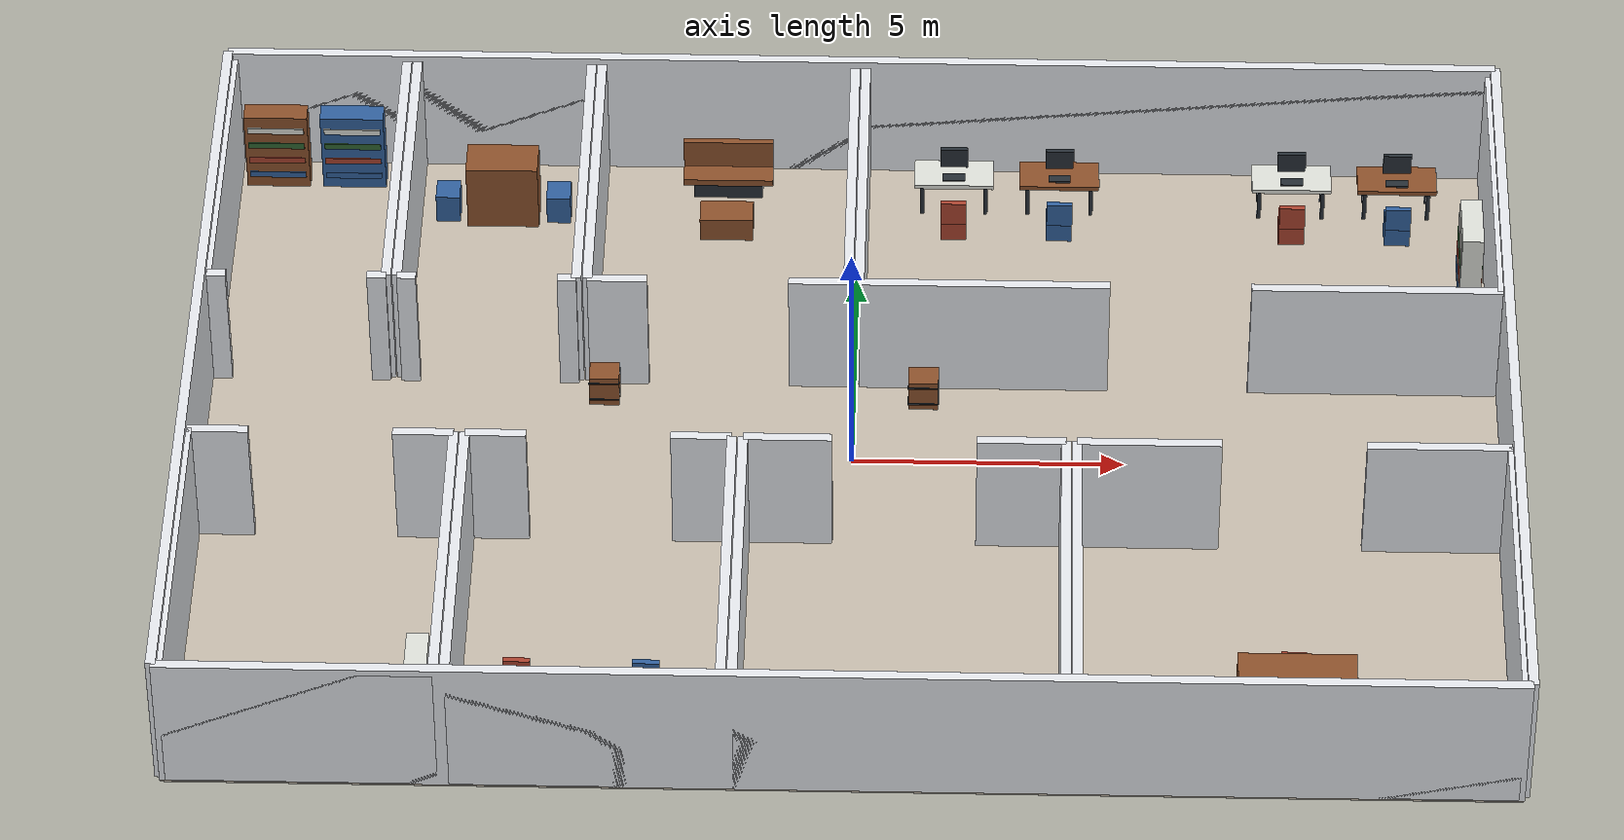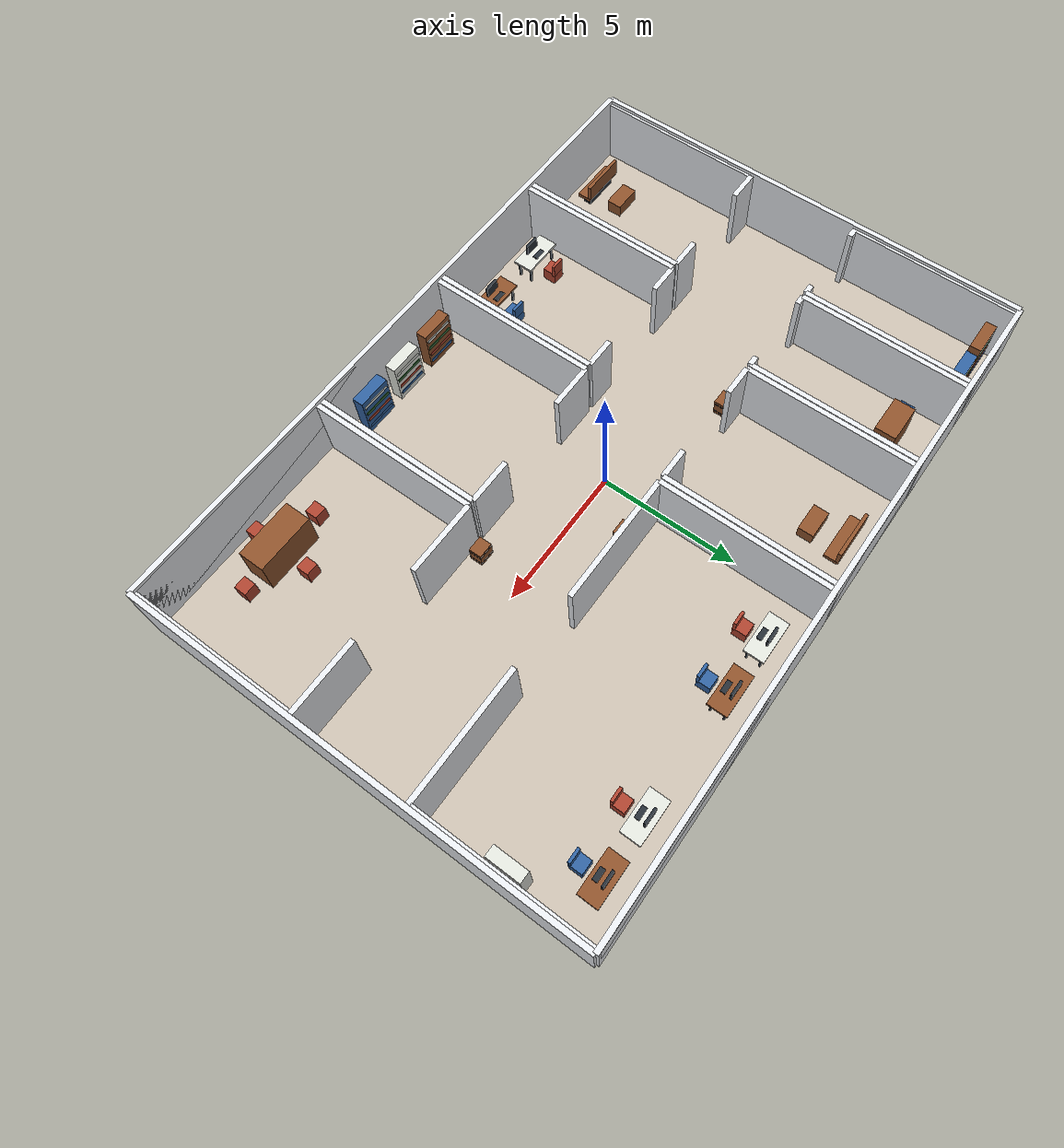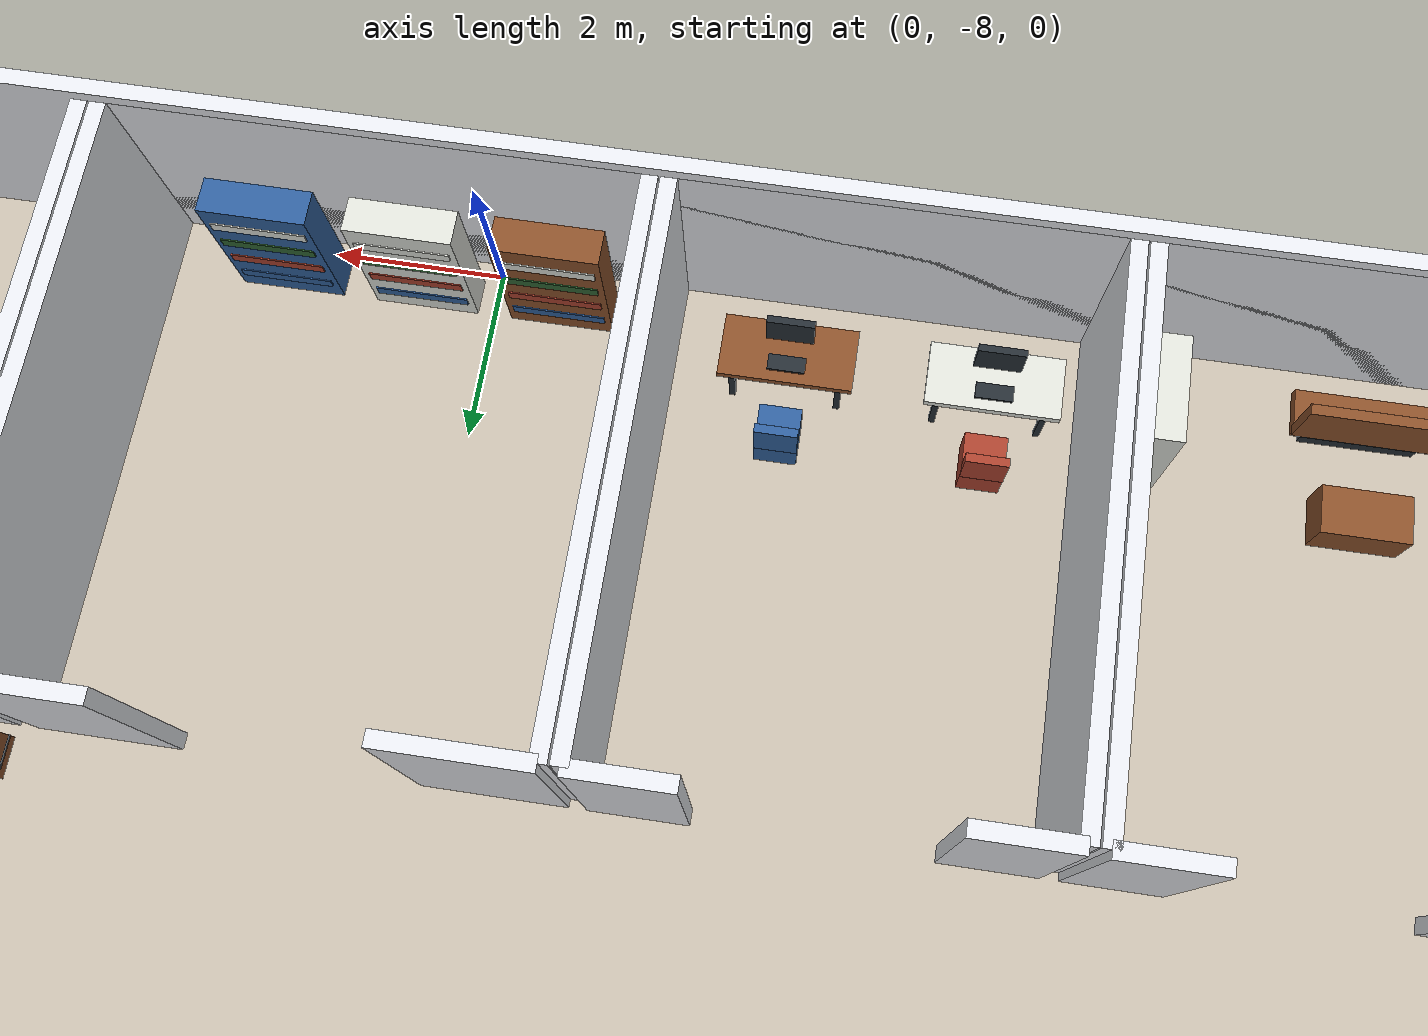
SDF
<?xml version='1.0' encoding='utf-8'?>
<sdf version="1.7">
  <world name="flat_M2">
    <gravity>0 0 -9.8</gravity>
    <plugin name="gazebo_ros_state" filename="libgazebo_ros_state.so">
      <ros>
        <namespace>/gazebo</namespace>
      </ros>
    </plugin>
    <physics name="ode_physics" type="ode">
      <max_step_size>0.001</max_step_size>
      <real_time_factor>1</real_time_factor>
      <real_time_update_rate>1000</real_time_update_rate>
      <ode>
        <solver>
          <type>quick</type>
          <iters>150</iters>
          <sor>1.3</sor>
        </solver>
        <constraints>
          <cfm>0</cfm>
          <erp>0.2</erp>
          <contact_max_correcting_vel>0.2</contact_max_correcting_vel>
          <contact_surface_layer>0.001</contact_surface_layer>
        </constraints>
      </ode>
    </physics>
    <light name="sun" type="directional">
      <pose>0 0 28 0 0 0</pose>
      <diffuse>0.92 0.91 0.88 1</diffuse>
      <specular>0.18 0.18 0.16 1</specular>
      <direction>-0.35 -0.28 -0.9</direction>
      <cast_shadows>true</cast_shadows>
    </light>
    <light name="fill" type="point">
      <pose>0 0 6 0 0 0</pose>
      <diffuse>0.35 0.36 0.34 1</diffuse>
      <specular>0.02 0.02 0.02 1</specular>
      <cast_shadows>false</cast_shadows>
      <attenuation>
        <range>80</range>
        <constant>0.5</constant>
        <linear>0.02</linear>
      </attenuation>
    </light>
    <scene>
      <ambient>0.50 0.49 0.47 1</ambient>
      <background>0.80 0.82 0.86 1</background>
    </scene>
    <gui fullscreen="false">
      <camera name="user_camera">
        <pose>16.8 -14.85 20.4 0 0.65 2.2</pose>
        <view_controller>orbit</view_controller>
      </camera>
    </gui>
    <model name="flat_M2_structure">
      <static>true</static>
      <link name="structure">
        <collision name="ground_floor_collision">
          <pose>0 0 -0.12 0 0 0</pose>
          <geometry>
            <box>
              <size>24 16.5 0.24</size>
            </box>
          </geometry>
          <max_contacts>40</max_contacts>
          <surface>
            <friction>
              <ode>
                <mu>2</mu>
                <mu2>2</mu2>
              </ode>
            </friction>
            <contact>
              <ode>
                <kp>1e7</kp>
                <kd>1000</kd>
                <max_vel>0.1</max_vel>
                <min_depth>0.001</min_depth>
              </ode>
            </contact>
          </surface>
        </collision>
        <visual name="ground_floor_visual">
          <pose>0 0 -0.12 0 0 0</pose>
          <geometry>
            <box>
              <size>24 16.5 0.24</size>
            </box>
          </geometry>
          <material>
            <ambient>0.78 0.74 0.68 1</ambient>
            <diffuse>0.78 0.74 0.68 1</diffuse>
          </material>
        </visual>
        <collision name="outer_south_wall_0_collision">
          <pose>0 -8.25 1.28 0 0 0</pose>
          <geometry>
            <box>
              <size>24 0.18 2.8</size>
            </box>
          </geometry>
          <max_contacts>40</max_contacts>
          <surface>
            <friction>
              <ode>
                <mu>2</mu>
                <mu2>2</mu2>
              </ode>
            </friction>
            <contact>
              <ode>
                <kp>1e7</kp>
                <kd>1000</kd>
                <max_vel>0.1</max_vel>
                <min_depth>0.001</min_depth>
              </ode>
            </contact>
          </surface>
        </collision>
        <visual name="outer_south_wall_0_visual">
          <pose>0 -8.25 1.28 0 0 0</pose>
          <geometry>
            <box>
              <size>24 0.18 2.8</size>
            </box>
          </geometry>
          <material>
            <ambient>0.90 0.91 0.93 1</ambient>
            <diffuse>0.90 0.91 0.93 1</diffuse>
          </material>
        </visual>
        <collision name="outer_north_wall_0_collision">
          <pose>0 8.25 1.28 0 0 0</pose>
          <geometry>
            <box>
              <size>24 0.18 2.8</size>
            </box>
          </geometry>
          <max_contacts>40</max_contacts>
          <surface>
            <friction>
              <ode>
                <mu>2</mu>
                <mu2>2</mu2>
              </ode>
            </friction>
            <contact>
              <ode>
                <kp>1e7</kp>
                <kd>1000</kd>
                <max_vel>0.1</max_vel>
                <min_depth>0.001</min_depth>
              </ode>
            </contact>
          </surface>
        </collision>
        <visual name="outer_north_wall_0_visual">
          <pose>0 8.25 1.28 0 0 0</pose>
          <geometry>
            <box>
              <size>24 0.18 2.8</size>
            </box>
          </geometry>
          <material>
            <ambient>0.90 0.91 0.93 1</ambient>
            <diffuse>0.90 0.91 0.93 1</diffuse>
          </material>
        </visual>
        <collision name="outer_west_wall_0_collision">
          <pose>-12 0 1.28 0 0 1.57079633</pose>
          <geometry>
            <box>
              <size>16.5 0.18 2.8</size>
            </box>
          </geometry>
          <max_contacts>40</max_contacts>
          <surface>
            <friction>
              <ode>
                <mu>2</mu>
                <mu2>2</mu2>
              </ode>
            </friction>
            <contact>
              <ode>
                <kp>1e7</kp>
                <kd>1000</kd>
                <max_vel>0.1</max_vel>
                <min_depth>0.001</min_depth>
              </ode>
            </contact>
          </surface>
        </collision>
        <visual name="outer_west_wall_0_visual">
          <pose>-12 0 1.28 0 0 1.57079633</pose>
          <geometry>
            <box>
              <size>16.5 0.18 2.8</size>
            </box>
          </geometry>
          <material>
            <ambient>0.90 0.91 0.93 1</ambient>
            <diffuse>0.90 0.91 0.93 1</diffuse>
          </material>
        </visual>
        <collision name="outer_east_wall_0_collision">
          <pose>12 0 1.28 0 0 1.57079633</pose>
          <geometry>
            <box>
              <size>16.5 0.18 2.8</size>
            </box>
          </geometry>
          <max_contacts>40</max_contacts>
          <surface>
            <friction>
              <ode>
                <mu>2</mu>
                <mu2>2</mu2>
              </ode>
            </friction>
            <contact>
              <ode>
                <kp>1e7</kp>
                <kd>1000</kd>
                <max_vel>0.1</max_vel>
                <min_depth>0.001</min_depth>
              </ode>
            </contact>
          </surface>
        </collision>
        <visual name="outer_east_wall_0_visual">
          <pose>12 0 1.28 0 0 1.57079633</pose>
          <geometry>
            <box>
              <size>16.5 0.18 2.8</size>
            </box>
          </geometry>
          <material>
            <ambient>0.90 0.91 0.93 1</ambient>
            <diffuse>0.90 0.91 0.93 1</diffuse>
          </material>
        </visual>
        <collision name="office_1_0_south_wall_0_collision">
          <pose>-11.725 2.1 1.225 0 0 0</pose>
          <geometry>
            <box>
              <size>0.35 0.18 2.65</size>
            </box>
          </geometry>
          <max_contacts>40</max_contacts>
          <surface>
            <friction>
              <ode>
                <mu>2</mu>
                <mu2>2</mu2>
              </ode>
            </friction>
            <contact>
              <ode>
                <kp>1e7</kp>
                <kd>1000</kd>
                <max_vel>0.1</max_vel>
                <min_depth>0.001</min_depth>
              </ode>
            </contact>
          </surface>
        </collision>
        <visual name="office_1_0_south_wall_0_visual">
          <pose>-11.725 2.1 1.225 0 0 0</pose>
          <geometry>
            <box>
              <size>0.35 0.18 2.65</size>
            </box>
          </geometry>
          <material>
            <ambient>0.90 0.91 0.93 1</ambient>
            <diffuse>0.90 0.91 0.93 1</diffuse>
          </material>
        </visual>
        <collision name="office_1_0_south_wall_1_collision">
          <pose>-8.775 2.1 1.225 0 0 0</pose>
          <geometry>
            <box>
              <size>0.35 0.18 2.65</size>
            </box>
          </geometry>
          <max_contacts>40</max_contacts>
          <surface>
            <friction>
              <ode>
                <mu>2</mu>
                <mu2>2</mu2>
              </ode>
            </friction>
            <contact>
              <ode>
                <kp>1e7</kp>
                <kd>1000</kd>
                <max_vel>0.1</max_vel>
                <min_depth>0.001</min_depth>
              </ode>
            </contact>
          </surface>
        </collision>
        <visual name="office_1_0_south_wall_1_visual">
          <pose>-8.775 2.1 1.225 0 0 0</pose>
          <geometry>
            <box>
              <size>0.35 0.18 2.65</size>
            </box>
          </geometry>
          <material>
            <ambient>0.90 0.91 0.93 1</ambient>
            <diffuse>0.90 0.91 0.93 1</diffuse>
          </material>
        </visual>
        <collision name="office_1_0_north_wall_0_collision">
          <pose>-10.25 8.25 1.225 0 0 0</pose>
          <geometry>
            <box>
              <size>3.3 0.18 2.65</size>
            </box>
          </geometry>
          <max_contacts>40</max_contacts>
          <surface>
            <friction>
              <ode>
                <mu>2</mu>
                <mu2>2</mu2>
              </ode>
            </friction>
            <contact>
              <ode>
                <kp>1e7</kp>
                <kd>1000</kd>
                <max_vel>0.1</max_vel>
                <min_depth>0.001</min_depth>
              </ode>
            </contact>
          </surface>
        </collision>
        <visual name="office_1_0_north_wall_0_visual">
          <pose>-10.25 8.25 1.225 0 0 0</pose>
          <geometry>
            <box>
              <size>3.3 0.18 2.65</size>
            </box>
          </geometry>
          <material>
            <ambient>0.90 0.91 0.93 1</ambient>
            <diffuse>0.90 0.91 0.93 1</diffuse>
          </material>
        </visual>
        <collision name="office_1_0_west_wall_0_collision">
          <pose>-11.9 5.175 1.225 0 0 1.57079633</pose>
          <geometry>
            <box>
              <size>6.15 0.18 2.65</size>
            </box>
          </geometry>
          <max_contacts>40</max_contacts>
          <surface>
            <friction>
              <ode>
                <mu>2</mu>
                <mu2>2</mu2>
              </ode>
            </friction>
            <contact>
              <ode>
                <kp>1e7</kp>
                <kd>1000</kd>
                <max_vel>0.1</max_vel>
                <min_depth>0.001</min_depth>
              </ode>
            </contact>
          </surface>
        </collision>
        <visual name="office_1_0_west_wall_0_visual">
          <pose>-11.9 5.175 1.225 0 0 1.57079633</pose>
          <geometry>
            <box>
              <size>6.15 0.18 2.65</size>
            </box>
          </geometry>
          <material>
            <ambient>0.90 0.91 0.93 1</ambient>
            <diffuse>0.90 0.91 0.93 1</diffuse>
          </material>
        </visual>
        <collision name="office_1_0_east_wall_0_collision">
          <pose>-8.6 5.175 1.225 0 0 1.57079633</pose>
          <geometry>
            <box>
              <size>6.15 0.18 2.65</size>
            </box>
          </geometry>
          <max_contacts>40</max_contacts>
          <surface>
            <friction>
              <ode>
                <mu>2</mu>
                <mu2>2</mu2>
              </ode>
            </friction>
            <contact>
              <ode>
                <kp>1e7</kp>
                <kd>1000</kd>
                <max_vel>0.1</max_vel>
                <min_depth>0.001</min_depth>
              </ode>
            </contact>
          </surface>
        </collision>
        <visual name="office_1_0_east_wall_0_visual">
          <pose>-8.6 5.175 1.225 0 0 1.57079633</pose>
          <geometry>
            <box>
              <size>6.15 0.18 2.65</size>
            </box>
          </geometry>
          <material>
            <ambient>0.90 0.91 0.93 1</ambient>
            <diffuse>0.90 0.91 0.93 1</diffuse>
          </material>
        </visual>
        <collision name="office_1_1_south_wall_0_collision">
          <pose>-8.225 2.1 1.225 0 0 0</pose>
          <geometry>
            <box>
              <size>0.35 0.18 2.65</size>
            </box>
          </geometry>
          <max_contacts>40</max_contacts>
          <surface>
            <friction>
              <ode>
                <mu>2</mu>
                <mu2>2</mu2>
              </ode>
            </friction>
            <contact>
              <ode>
                <kp>1e7</kp>
                <kd>1000</kd>
                <max_vel>0.1</max_vel>
                <min_depth>0.001</min_depth>
              </ode>
            </contact>
          </surface>
        </collision>
        <visual name="office_1_1_south_wall_0_visual">
          <pose>-8.225 2.1 1.225 0 0 0</pose>
          <geometry>
            <box>
              <size>0.35 0.18 2.65</size>
            </box>
          </geometry>
          <material>
            <ambient>0.90 0.91 0.93 1</ambient>
            <diffuse>0.90 0.91 0.93 1</diffuse>
          </material>
        </visual>
        <collision name="office_1_1_south_wall_1_collision">
          <pose>-5.275 2.1 1.225 0 0 0</pose>
          <geometry>
            <box>
              <size>0.35 0.18 2.65</size>
            </box>
          </geometry>
          <max_contacts>40</max_contacts>
          <surface>
            <friction>
              <ode>
                <mu>2</mu>
                <mu2>2</mu2>
              </ode>
            </friction>
            <contact>
              <ode>
                <kp>1e7</kp>
                <kd>1000</kd>
                <max_vel>0.1</max_vel>
                <min_depth>0.001</min_depth>
              </ode>
            </contact>
          </surface>
        </collision>
        <visual name="office_1_1_south_wall_1_visual">
          <pose>-5.275 2.1 1.225 0 0 0</pose>
          <geometry>
            <box>
              <size>0.35 0.18 2.65</size>
            </box>
          </geometry>
          <material>
            <ambient>0.90 0.91 0.93 1</ambient>
            <diffuse>0.90 0.91 0.93 1</diffuse>
          </material>
        </visual>
        <collision name="office_1_1_north_wall_0_collision">
          <pose>-6.75 8.25 1.225 0 0 0</pose>
          <geometry>
            <box>
              <size>3.3 0.18 2.65</size>
            </box>
          </geometry>
          <max_contacts>40</max_contacts>
          <surface>
            <friction>
              <ode>
                <mu>2</mu>
                <mu2>2</mu2>
              </ode>
            </friction>
            <contact>
              <ode>
                <kp>1e7</kp>
                <kd>1000</kd>
                <max_vel>0.1</max_vel>
                <min_depth>0.001</min_depth>
              </ode>
            </contact>
          </surface>
        </collision>
        <visual name="office_1_1_north_wall_0_visual">
          <pose>-6.75 8.25 1.225 0 0 0</pose>
          <geometry>
            <box>
              <size>3.3 0.18 2.65</size>
            </box>
          </geometry>
          <material>
            <ambient>0.90 0.91 0.93 1</ambient>
            <diffuse>0.90 0.91 0.93 1</diffuse>
          </material>
        </visual>
        <collision name="office_1_1_west_wall_0_collision">
          <pose>-8.4 5.175 1.225 0 0 1.57079633</pose>
          <geometry>
            <box>
              <size>6.15 0.18 2.65</size>
            </box>
          </geometry>
          <max_contacts>40</max_contacts>
          <surface>
            <friction>
              <ode>
                <mu>2</mu>
                <mu2>2</mu2>
              </ode>
            </friction>
            <contact>
              <ode>
                <kp>1e7</kp>
                <kd>1000</kd>
                <max_vel>0.1</max_vel>
                <min_depth>0.001</min_depth>
              </ode>
            </contact>
          </surface>
        </collision>
        <visual name="office_1_1_west_wall_0_visual">
          <pose>-8.4 5.175 1.225 0 0 1.57079633</pose>
          <geometry>
            <box>
              <size>6.15 0.18 2.65</size>
            </box>
          </geometry>
          <material>
            <ambient>0.90 0.91 0.93 1</ambient>
            <diffuse>0.90 0.91 0.93 1</diffuse>
          </material>
        </visual>
        <collision name="office_1_1_east_wall_0_collision">
          <pose>-5.1 5.175 1.225 0 0 1.57079633</pose>
          <geometry>
            <box>
              <size>6.15 0.18 2.65</size>
            </box>
          </geometry>
          <max_contacts>40</max_contacts>
          <surface>
            <friction>
              <ode>
                <mu>2</mu>
                <mu2>2</mu2>
              </ode>
            </friction>
            <contact>
              <ode>
                <kp>1e7</kp>
                <kd>1000</kd>
                <max_vel>0.1</max_vel>
                <min_depth>0.001</min_depth>
              </ode>
            </contact>
          </surface>
        </collision>
        <visual name="office_1_1_east_wall_0_visual">
          <pose>-5.1 5.175 1.225 0 0 1.57079633</pose>
          <geometry>
            <box>
              <size>6.15 0.18 2.65</size>
            </box>
          </geometry>
          <material>
            <ambient>0.90 0.91 0.93 1</ambient>
            <diffuse>0.90 0.91 0.93 1</diffuse>
          </material>
        </visual>
        <collision name="office_1_2_south_wall_0_collision">
          <pose>-4.35 2.1 1.225 0 0 0</pose>
          <geometry>
            <box>
              <size>1.1 0.18 2.65</size>
            </box>
          </geometry>
          <max_contacts>40</max_contacts>
          <surface>
            <friction>
              <ode>
                <mu>2</mu>
                <mu2>2</mu2>
              </ode>
            </friction>
            <contact>
              <ode>
                <kp>1e7</kp>
                <kd>1000</kd>
                <max_vel>0.1</max_vel>
                <min_depth>0.001</min_depth>
              </ode>
            </contact>
          </surface>
        </collision>
        <visual name="office_1_2_south_wall_0_visual">
          <pose>-4.35 2.1 1.225 0 0 0</pose>
          <geometry>
            <box>
              <size>1.1 0.18 2.65</size>
            </box>
          </geometry>
          <material>
            <ambient>0.90 0.91 0.93 1</ambient>
            <diffuse>0.90 0.91 0.93 1</diffuse>
          </material>
        </visual>
        <collision name="office_1_2_south_wall_1_collision">
          <pose>-0.65 2.1 1.225 0 0 0</pose>
          <geometry>
            <box>
              <size>1.1 0.18 2.65</size>
            </box>
          </geometry>
          <max_contacts>40</max_contacts>
          <surface>
            <friction>
              <ode>
                <mu>2</mu>
                <mu2>2</mu2>
              </ode>
            </friction>
            <contact>
              <ode>
                <kp>1e7</kp>
                <kd>1000</kd>
                <max_vel>0.1</max_vel>
                <min_depth>0.001</min_depth>
              </ode>
            </contact>
          </surface>
        </collision>
        <visual name="office_1_2_south_wall_1_visual">
          <pose>-0.65 2.1 1.225 0 0 0</pose>
          <geometry>
            <box>
              <size>1.1 0.18 2.65</size>
            </box>
          </geometry>
          <material>
            <ambient>0.90 0.91 0.93 1</ambient>
            <diffuse>0.90 0.91 0.93 1</diffuse>
          </material>
        </visual>
        <collision name="office_1_2_north_wall_0_collision">
          <pose>-2.5 8.25 1.225 0 0 0</pose>
          <geometry>
            <box>
              <size>4.8 0.18 2.65</size>
            </box>
          </geometry>
          <max_contacts>40</max_contacts>
          <surface>
            <friction>
              <ode>
                <mu>2</mu>
                <mu2>2</mu2>
              </ode>
            </friction>
            <contact>
              <ode>
                <kp>1e7</kp>
                <kd>1000</kd>
                <max_vel>0.1</max_vel>
                <min_depth>0.001</min_depth>
              </ode>
            </contact>
          </surface>
        </collision>
        <visual name="office_1_2_north_wall_0_visual">
          <pose>-2.5 8.25 1.225 0 0 0</pose>
          <geometry>
            <box>
              <size>4.8 0.18 2.65</size>
            </box>
          </geometry>
          <material>
            <ambient>0.90 0.91 0.93 1</ambient>
            <diffuse>0.90 0.91 0.93 1</diffuse>
          </material>
        </visual>
        <collision name="office_1_2_west_wall_0_collision">
          <pose>-4.9 5.175 1.225 0 0 1.57079633</pose>
          <geometry>
            <box>
              <size>6.15 0.18 2.65</size>
            </box>
          </geometry>
          <max_contacts>40</max_contacts>
          <surface>
            <friction>
              <ode>
                <mu>2</mu>
                <mu2>2</mu2>
              </ode>
            </friction>
            <contact>
              <ode>
                <kp>1e7</kp>
                <kd>1000</kd>
                <max_vel>0.1</max_vel>
                <min_depth>0.001</min_depth>
              </ode>
            </contact>
          </surface>
        </collision>
        <visual name="office_1_2_west_wall_0_visual">
          <pose>-4.9 5.175 1.225 0 0 1.57079633</pose>
          <geometry>
            <box>
              <size>6.15 0.18 2.65</size>
            </box>
          </geometry>
          <material>
            <ambient>0.90 0.91 0.93 1</ambient>
            <diffuse>0.90 0.91 0.93 1</diffuse>
          </material>
        </visual>
        <collision name="office_1_2_east_wall_0_collision">
          <pose>-0.1 5.175 1.225 0 0 1.57079633</pose>
          <geometry>
            <box>
              <size>6.15 0.18 2.65</size>
            </box>
          </geometry>
          <max_contacts>40</max_contacts>
          <surface>
            <friction>
              <ode>
                <mu>2</mu>
                <mu2>2</mu2>
              </ode>
            </friction>
            <contact>
              <ode>
                <kp>1e7</kp>
                <kd>1000</kd>
                <max_vel>0.1</max_vel>
                <min_depth>0.001</min_depth>
              </ode>
            </contact>
          </surface>
        </collision>
        <visual name="office_1_2_east_wall_0_visual">
          <pose>-0.1 5.175 1.225 0 0 1.57079633</pose>
          <geometry>
            <box>
              <size>6.15 0.18 2.65</size>
            </box>
          </geometry>
          <material>
            <ambient>0.90 0.91 0.93 1</ambient>
            <diffuse>0.90 0.91 0.93 1</diffuse>
          </material>
        </visual>
        <collision name="office_1_3_south_wall_0_collision">
          <pose>2.4 2.1 1.225 0 0 0</pose>
          <geometry>
            <box>
              <size>4.6 0.18 2.65</size>
            </box>
          </geometry>
          <max_contacts>40</max_contacts>
          <surface>
            <friction>
              <ode>
                <mu>2</mu>
                <mu2>2</mu2>
              </ode>
            </friction>
            <contact>
              <ode>
                <kp>1e7</kp>
                <kd>1000</kd>
                <max_vel>0.1</max_vel>
                <min_depth>0.001</min_depth>
              </ode>
            </contact>
          </surface>
        </collision>
        <visual name="office_1_3_south_wall_0_visual">
          <pose>2.4 2.1 1.225 0 0 0</pose>
          <geometry>
            <box>
              <size>4.6 0.18 2.65</size>
            </box>
          </geometry>
          <material>
            <ambient>0.90 0.91 0.93 1</ambient>
            <diffuse>0.90 0.91 0.93 1</diffuse>
          </material>
        </visual>
        <collision name="office_1_3_south_wall_1_collision">
          <pose>9.6 2.1 1.225 0 0 0</pose>
          <geometry>
            <box>
              <size>4.6 0.18 2.65</size>
            </box>
          </geometry>
          <max_contacts>40</max_contacts>
          <surface>
            <friction>
              <ode>
                <mu>2</mu>
                <mu2>2</mu2>
              </ode>
            </friction>
            <contact>
              <ode>
                <kp>1e7</kp>
                <kd>1000</kd>
                <max_vel>0.1</max_vel>
                <min_depth>0.001</min_depth>
              </ode>
            </contact>
          </surface>
        </collision>
        <visual name="office_1_3_south_wall_1_visual">
          <pose>9.6 2.1 1.225 0 0 0</pose>
          <geometry>
            <box>
              <size>4.6 0.18 2.65</size>
            </box>
          </geometry>
          <material>
            <ambient>0.90 0.91 0.93 1</ambient>
            <diffuse>0.90 0.91 0.93 1</diffuse>
          </material>
        </visual>
        <collision name="office_1_3_north_wall_0_collision">
          <pose>6 8.25 1.225 0 0 0</pose>
          <geometry>
            <box>
              <size>11.8 0.18 2.65</size>
            </box>
          </geometry>
          <max_contacts>40</max_contacts>
          <surface>
            <friction>
              <ode>
                <mu>2</mu>
                <mu2>2</mu2>
              </ode>
            </friction>
            <contact>
              <ode>
                <kp>1e7</kp>
                <kd>1000</kd>
                <max_vel>0.1</max_vel>
                <min_depth>0.001</min_depth>
              </ode>
            </contact>
          </surface>
        </collision>
        <visual name="office_1_3_north_wall_0_visual">
          <pose>6 8.25 1.225 0 0 0</pose>
          <geometry>
            <box>
              <size>11.8 0.18 2.65</size>
            </box>
          </geometry>
          <material>
            <ambient>0.90 0.91 0.93 1</ambient>
            <diffuse>0.90 0.91 0.93 1</diffuse>
          </material>
        </visual>
        <collision name="office_1_3_west_wall_0_collision">
          <pose>0.1 5.175 1.225 0 0 1.57079633</pose>
          <geometry>
            <box>
              <size>6.15 0.18 2.65</size>
            </box>
          </geometry>
          <max_contacts>40</max_contacts>
          <surface>
            <friction>
              <ode>
                <mu>2</mu>
                <mu2>2</mu2>
              </ode>
            </friction>
            <contact>
              <ode>
                <kp>1e7</kp>
                <kd>1000</kd>
                <max_vel>0.1</max_vel>
                <min_depth>0.001</min_depth>
              </ode>
            </contact>
          </surface>
        </collision>
        <visual name="office_1_3_west_wall_0_visual">
          <pose>0.1 5.175 1.225 0 0 1.57079633</pose>
          <geometry>
            <box>
              <size>6.15 0.18 2.65</size>
            </box>
          </geometry>
          <material>
            <ambient>0.90 0.91 0.93 1</ambient>
            <diffuse>0.90 0.91 0.93 1</diffuse>
          </material>
        </visual>
        <collision name="office_1_3_east_wall_0_collision">
          <pose>11.9 5.175 1.225 0 0 1.57079633</pose>
          <geometry>
            <box>
              <size>6.15 0.18 2.65</size>
            </box>
          </geometry>
          <max_contacts>40</max_contacts>
          <surface>
            <friction>
              <ode>
                <mu>2</mu>
                <mu2>2</mu2>
              </ode>
            </friction>
            <contact>
              <ode>
                <kp>1e7</kp>
                <kd>1000</kd>
                <max_vel>0.1</max_vel>
                <min_depth>0.001</min_depth>
              </ode>
            </contact>
          </surface>
        </collision>
        <visual name="office_1_3_east_wall_0_visual">
          <pose>11.9 5.175 1.225 0 0 1.57079633</pose>
          <geometry>
            <box>
              <size>6.15 0.18 2.65</size>
            </box>
          </geometry>
          <material>
            <ambient>0.90 0.91 0.93 1</ambient>
            <diffuse>0.90 0.91 0.93 1</diffuse>
          </material>
        </visual>
        <collision name="office_-1_0_south_wall_0_collision">
          <pose>-9.5 -8.25 1.225 0 0 0</pose>
          <geometry>
            <box>
              <size>4.8 0.18 2.65</size>
            </box>
          </geometry>
          <max_contacts>40</max_contacts>
          <surface>
            <friction>
              <ode>
                <mu>2</mu>
                <mu2>2</mu2>
              </ode>
            </friction>
            <contact>
              <ode>
                <kp>1e7</kp>
                <kd>1000</kd>
                <max_vel>0.1</max_vel>
                <min_depth>0.001</min_depth>
              </ode>
            </contact>
          </surface>
        </collision>
        <visual name="office_-1_0_south_wall_0_visual">
          <pose>-9.5 -8.25 1.225 0 0 0</pose>
          <geometry>
            <box>
              <size>4.8 0.18 2.65</size>
            </box>
          </geometry>
          <material>
            <ambient>0.90 0.91 0.93 1</ambient>
            <diffuse>0.90 0.91 0.93 1</diffuse>
          </material>
        </visual>
        <collision name="office_-1_0_north_wall_0_collision">
          <pose>-11.35 -2.1 1.225 0 0 0</pose>
          <geometry>
            <box>
              <size>1.1 0.18 2.65</size>
            </box>
          </geometry>
          <max_contacts>40</max_contacts>
          <surface>
            <friction>
              <ode>
                <mu>2</mu>
                <mu2>2</mu2>
              </ode>
            </friction>
            <contact>
              <ode>
                <kp>1e7</kp>
                <kd>1000</kd>
                <max_vel>0.1</max_vel>
                <min_depth>0.001</min_depth>
              </ode>
            </contact>
          </surface>
        </collision>
        <visual name="office_-1_0_north_wall_0_visual">
          <pose>-11.35 -2.1 1.225 0 0 0</pose>
          <geometry>
            <box>
              <size>1.1 0.18 2.65</size>
            </box>
          </geometry>
          <material>
            <ambient>0.90 0.91 0.93 1</ambient>
            <diffuse>0.90 0.91 0.93 1</diffuse>
          </material>
        </visual>
        <collision name="office_-1_0_north_wall_1_collision">
          <pose>-7.65 -2.1 1.225 0 0 0</pose>
          <geometry>
            <box>
              <size>1.1 0.18 2.65</size>
            </box>
          </geometry>
          <max_contacts>40</max_contacts>
          <surface>
            <friction>
              <ode>
                <mu>2</mu>
                <mu2>2</mu2>
              </ode>
            </friction>
            <contact>
              <ode>
                <kp>1e7</kp>
                <kd>1000</kd>
                <max_vel>0.1</max_vel>
                <min_depth>0.001</min_depth>
              </ode>
            </contact>
          </surface>
        </collision>
        <visual name="office_-1_0_north_wall_1_visual">
          <pose>-7.65 -2.1 1.225 0 0 0</pose>
          <geometry>
            <box>
              <size>1.1 0.18 2.65</size>
            </box>
          </geometry>
          <material>
            <ambient>0.90 0.91 0.93 1</ambient>
            <diffuse>0.90 0.91 0.93 1</diffuse>
          </material>
        </visual>
        <collision name="office_-1_0_west_wall_0_collision">
          <pose>-11.9 -5.175 1.225 0 0 1.57079633</pose>
          <geometry>
            <box>
              <size>6.15 0.18 2.65</size>
            </box>
          </geometry>
          <max_contacts>40</max_contacts>
          <surface>
            <friction>
              <ode>
                <mu>2</mu>
                <mu2>2</mu2>
              </ode>
            </friction>
            <contact>
              <ode>
                <kp>1e7</kp>
                <kd>1000</kd>
                <max_vel>0.1</max_vel>
                <min_depth>0.001</min_depth>
              </ode>
            </contact>
          </surface>
        </collision>
        <visual name="office_-1_0_west_wall_0_visual">
          <pose>-11.9 -5.175 1.225 0 0 1.57079633</pose>
          <geometry>
            <box>
              <size>6.15 0.18 2.65</size>
            </box>
          </geometry>
          <material>
            <ambient>0.90 0.91 0.93 1</ambient>
            <diffuse>0.90 0.91 0.93 1</diffuse>
          </material>
        </visual>
        <collision name="office_-1_0_east_wall_0_collision">
          <pose>-7.1 -5.175 1.225 0 0 1.57079633</pose>
          <geometry>
            <box>
              <size>6.15 0.18 2.65</size>
            </box>
          </geometry>
          <max_contacts>40</max_contacts>
          <surface>
            <friction>
              <ode>
                <mu>2</mu>
                <mu2>2</mu2>
              </ode>
            </friction>
            <contact>
              <ode>
                <kp>1e7</kp>
                <kd>1000</kd>
                <max_vel>0.1</max_vel>
                <min_depth>0.001</min_depth>
              </ode>
            </contact>
          </surface>
        </collision>
        <visual name="office_-1_0_east_wall_0_visual">
          <pose>-7.1 -5.175 1.225 0 0 1.57079633</pose>
          <geometry>
            <box>
              <size>6.15 0.18 2.65</size>
            </box>
          </geometry>
          <material>
            <ambient>0.90 0.91 0.93 1</ambient>
            <diffuse>0.90 0.91 0.93 1</diffuse>
          </material>
        </visual>
        <collision name="office_-1_1_south_wall_0_collision">
          <pose>-4.5 -8.25 1.225 0 0 0</pose>
          <geometry>
            <box>
              <size>4.8 0.18 2.65</size>
            </box>
          </geometry>
          <max_contacts>40</max_contacts>
          <surface>
            <friction>
              <ode>
                <mu>2</mu>
                <mu2>2</mu2>
              </ode>
            </friction>
            <contact>
              <ode>
                <kp>1e7</kp>
                <kd>1000</kd>
                <max_vel>0.1</max_vel>
                <min_depth>0.001</min_depth>
              </ode>
            </contact>
          </surface>
        </collision>
        <visual name="office_-1_1_south_wall_0_visual">
          <pose>-4.5 -8.25 1.225 0 0 0</pose>
          <geometry>
            <box>
              <size>4.8 0.18 2.65</size>
            </box>
          </geometry>
          <material>
            <ambient>0.90 0.91 0.93 1</ambient>
            <diffuse>0.90 0.91 0.93 1</diffuse>
          </material>
        </visual>
        <collision name="office_-1_1_north_wall_0_collision">
          <pose>-6.35 -2.1 1.225 0 0 0</pose>
          <geometry>
            <box>
              <size>1.1 0.18 2.65</size>
            </box>
          </geometry>
          <max_contacts>40</max_contacts>
          <surface>
            <friction>
              <ode>
                <mu>2</mu>
                <mu2>2</mu2>
              </ode>
            </friction>
            <contact>
              <ode>
                <kp>1e7</kp>
                <kd>1000</kd>
                <max_vel>0.1</max_vel>
                <min_depth>0.001</min_depth>
              </ode>
            </contact>
          </surface>
        </collision>
        <visual name="office_-1_1_north_wall_0_visual">
          <pose>-6.35 -2.1 1.225 0 0 0</pose>
          <geometry>
            <box>
              <size>1.1 0.18 2.65</size>
            </box>
          </geometry>
          <material>
            <ambient>0.90 0.91 0.93 1</ambient>
            <diffuse>0.90 0.91 0.93 1</diffuse>
          </material>
        </visual>
        <collision name="office_-1_1_north_wall_1_collision">
          <pose>-2.65 -2.1 1.225 0 0 0</pose>
          <geometry>
            <box>
              <size>1.1 0.18 2.65</size>
            </box>
          </geometry>
          <max_contacts>40</max_contacts>
          <surface>
            <friction>
              <ode>
                <mu>2</mu>
                <mu2>2</mu2>
              </ode>
            </friction>
            <contact>
              <ode>
                <kp>1e7</kp>
                <kd>1000</kd>
                <max_vel>0.1</max_vel>
                <min_depth>0.001</min_depth>
              </ode>
            </contact>
          </surface>
        </collision>
        <visual name="office_-1_1_north_wall_1_visual">
          <pose>-2.65 -2.1 1.225 0 0 0</pose>
          <geometry>
            <box>
              <size>1.1 0.18 2.65</size>
            </box>
          </geometry>
          <material>
            <ambient>0.90 0.91 0.93 1</ambient>
            <diffuse>0.90 0.91 0.93 1</diffuse>
          </material>
        </visual>
        <collision name="office_-1_1_west_wall_0_collision">
          <pose>-6.9 -5.175 1.225 0 0 1.57079633</pose>
          <geometry>
            <box>
              <size>6.15 0.18 2.65</size>
            </box>
          </geometry>
          <max_contacts>40</max_contacts>
          <surface>
            <friction>
              <ode>
                <mu>2</mu>
                <mu2>2</mu2>
              </ode>
            </friction>
            <contact>
              <ode>
                <kp>1e7</kp>
                <kd>1000</kd>
                <max_vel>0.1</max_vel>
                <min_depth>0.001</min_depth>
              </ode>
            </contact>
          </surface>
        </collision>
        <visual name="office_-1_1_west_wall_0_visual">
          <pose>-6.9 -5.175 1.225 0 0 1.57079633</pose>
          <geometry>
            <box>
              <size>6.15 0.18 2.65</size>
            </box>
          </geometry>
          <material>
            <ambient>0.90 0.91 0.93 1</ambient>
            <diffuse>0.90 0.91 0.93 1</diffuse>
          </material>
        </visual>
        <collision name="office_-1_1_east_wall_0_collision">
          <pose>-2.1 -5.175 1.225 0 0 1.57079633</pose>
          <geometry>
            <box>
              <size>6.15 0.18 2.65</size>
            </box>
          </geometry>
          <max_contacts>40</max_contacts>
          <surface>
            <friction>
              <ode>
                <mu>2</mu>
                <mu2>2</mu2>
              </ode>
            </friction>
            <contact>
              <ode>
                <kp>1e7</kp>
                <kd>1000</kd>
                <max_vel>0.1</max_vel>
                <min_depth>0.001</min_depth>
              </ode>
            </contact>
          </surface>
        </collision>
        <visual name="office_-1_1_east_wall_0_visual">
          <pose>-2.1 -5.175 1.225 0 0 1.57079633</pose>
          <geometry>
            <box>
              <size>6.15 0.18 2.65</size>
            </box>
          </geometry>
          <material>
            <ambient>0.90 0.91 0.93 1</ambient>
            <diffuse>0.90 0.91 0.93 1</diffuse>
          </material>
        </visual>
        <collision name="office_-1_2_south_wall_0_collision">
          <pose>1 -8.25 1.225 0 0 0</pose>
          <geometry>
            <box>
              <size>5.8 0.18 2.65</size>
            </box>
          </geometry>
          <max_contacts>40</max_contacts>
          <surface>
            <friction>
              <ode>
                <mu>2</mu>
                <mu2>2</mu2>
              </ode>
            </friction>
            <contact>
              <ode>
                <kp>1e7</kp>
                <kd>1000</kd>
                <max_vel>0.1</max_vel>
                <min_depth>0.001</min_depth>
              </ode>
            </contact>
          </surface>
        </collision>
        <visual name="office_-1_2_south_wall_0_visual">
          <pose>1 -8.25 1.225 0 0 0</pose>
          <geometry>
            <box>
              <size>5.8 0.18 2.65</size>
            </box>
          </geometry>
          <material>
            <ambient>0.90 0.91 0.93 1</ambient>
            <diffuse>0.90 0.91 0.93 1</diffuse>
          </material>
        </visual>
        <collision name="office_-1_2_north_wall_0_collision">
          <pose>-1.1 -2.1 1.225 0 0 0</pose>
          <geometry>
            <box>
              <size>1.6 0.18 2.65</size>
            </box>
          </geometry>
          <max_contacts>40</max_contacts>
          <surface>
            <friction>
              <ode>
                <mu>2</mu>
                <mu2>2</mu2>
              </ode>
            </friction>
            <contact>
              <ode>
                <kp>1e7</kp>
                <kd>1000</kd>
                <max_vel>0.1</max_vel>
                <min_depth>0.001</min_depth>
              </ode>
            </contact>
          </surface>
        </collision>
        <visual name="office_-1_2_north_wall_0_visual">
          <pose>-1.1 -2.1 1.225 0 0 0</pose>
          <geometry>
            <box>
              <size>1.6 0.18 2.65</size>
            </box>
          </geometry>
          <material>
            <ambient>0.90 0.91 0.93 1</ambient>
            <diffuse>0.90 0.91 0.93 1</diffuse>
          </material>
        </visual>
        <collision name="office_-1_2_north_wall_1_collision">
          <pose>3.1 -2.1 1.225 0 0 0</pose>
          <geometry>
            <box>
              <size>1.6 0.18 2.65</size>
            </box>
          </geometry>
          <max_contacts>40</max_contacts>
          <surface>
            <friction>
              <ode>
                <mu>2</mu>
                <mu2>2</mu2>
              </ode>
            </friction>
            <contact>
              <ode>
                <kp>1e7</kp>
                <kd>1000</kd>
                <max_vel>0.1</max_vel>
                <min_depth>0.001</min_depth>
              </ode>
            </contact>
          </surface>
        </collision>
        <visual name="office_-1_2_north_wall_1_visual">
          <pose>3.1 -2.1 1.225 0 0 0</pose>
          <geometry>
            <box>
              <size>1.6 0.18 2.65</size>
            </box>
          </geometry>
          <material>
            <ambient>0.90 0.91 0.93 1</ambient>
            <diffuse>0.90 0.91 0.93 1</diffuse>
          </material>
        </visual>
        <collision name="office_-1_2_west_wall_0_collision">
          <pose>-1.9 -5.175 1.225 0 0 1.57079633</pose>
          <geometry>
            <box>
              <size>6.15 0.18 2.65</size>
            </box>
          </geometry>
          <max_contacts>40</max_contacts>
          <surface>
            <friction>
              <ode>
                <mu>2</mu>
                <mu2>2</mu2>
              </ode>
            </friction>
            <contact>
              <ode>
                <kp>1e7</kp>
                <kd>1000</kd>
                <max_vel>0.1</max_vel>
                <min_depth>0.001</min_depth>
              </ode>
            </contact>
          </surface>
        </collision>
        <visual name="office_-1_2_west_wall_0_visual">
          <pose>-1.9 -5.175 1.225 0 0 1.57079633</pose>
          <geometry>
            <box>
              <size>6.15 0.18 2.65</size>
            </box>
          </geometry>
          <material>
            <ambient>0.90 0.91 0.93 1</ambient>
            <diffuse>0.90 0.91 0.93 1</diffuse>
          </material>
        </visual>
        <collision name="office_-1_2_east_wall_0_collision">
          <pose>3.9 -5.175 1.225 0 0 1.57079633</pose>
          <geometry>
            <box>
              <size>6.15 0.18 2.65</size>
            </box>
          </geometry>
          <max_contacts>40</max_contacts>
          <surface>
            <friction>
              <ode>
                <mu>2</mu>
                <mu2>2</mu2>
              </ode>
            </friction>
            <contact>
              <ode>
                <kp>1e7</kp>
                <kd>1000</kd>
                <max_vel>0.1</max_vel>
                <min_depth>0.001</min_depth>
              </ode>
            </contact>
          </surface>
        </collision>
        <visual name="office_-1_2_east_wall_0_visual">
          <pose>3.9 -5.175 1.225 0 0 1.57079633</pose>
          <geometry>
            <box>
              <size>6.15 0.18 2.65</size>
            </box>
          </geometry>
          <material>
            <ambient>0.90 0.91 0.93 1</ambient>
            <diffuse>0.90 0.91 0.93 1</diffuse>
          </material>
        </visual>
        <collision name="office_-1_3_south_wall_0_collision">
          <pose>8 -8.25 1.225 0 0 0</pose>
          <geometry>
            <box>
              <size>7.8 0.18 2.65</size>
            </box>
          </geometry>
          <max_contacts>40</max_contacts>
          <surface>
            <friction>
              <ode>
                <mu>2</mu>
                <mu2>2</mu2>
              </ode>
            </friction>
            <contact>
              <ode>
                <kp>1e7</kp>
                <kd>1000</kd>
                <max_vel>0.1</max_vel>
                <min_depth>0.001</min_depth>
              </ode>
            </contact>
          </surface>
        </collision>
        <visual name="office_-1_3_south_wall_0_visual">
          <pose>8 -8.25 1.225 0 0 0</pose>
          <geometry>
            <box>
              <size>7.8 0.18 2.65</size>
            </box>
          </geometry>
          <material>
            <ambient>0.90 0.91 0.93 1</ambient>
            <diffuse>0.90 0.91 0.93 1</diffuse>
          </material>
        </visual>
        <collision name="office_-1_3_north_wall_0_collision">
          <pose>5.4 -2.1 1.225 0 0 0</pose>
          <geometry>
            <box>
              <size>2.6 0.18 2.65</size>
            </box>
          </geometry>
          <max_contacts>40</max_contacts>
          <surface>
            <friction>
              <ode>
                <mu>2</mu>
                <mu2>2</mu2>
              </ode>
            </friction>
            <contact>
              <ode>
                <kp>1e7</kp>
                <kd>1000</kd>
                <max_vel>0.1</max_vel>
                <min_depth>0.001</min_depth>
              </ode>
            </contact>
          </surface>
        </collision>
        <visual name="office_-1_3_north_wall_0_visual">
          <pose>5.4 -2.1 1.225 0 0 0</pose>
          <geometry>
            <box>
              <size>2.6 0.18 2.65</size>
            </box>
          </geometry>
          <material>
            <ambient>0.90 0.91 0.93 1</ambient>
            <diffuse>0.90 0.91 0.93 1</diffuse>
          </material>
        </visual>
        <collision name="office_-1_3_north_wall_1_collision">
          <pose>10.6 -2.1 1.225 0 0 0</pose>
          <geometry>
            <box>
              <size>2.6 0.18 2.65</size>
            </box>
          </geometry>
          <max_contacts>40</max_contacts>
          <surface>
            <friction>
              <ode>
                <mu>2</mu>
                <mu2>2</mu2>
              </ode>
            </friction>
            <contact>
              <ode>
                <kp>1e7</kp>
                <kd>1000</kd>
                <max_vel>0.1</max_vel>
                <min_depth>0.001</min_depth>
              </ode>
            </contact>
          </surface>
        </collision>
        <visual name="office_-1_3_north_wall_1_visual">
          <pose>10.6 -2.1 1.225 0 0 0</pose>
          <geometry>
            <box>
              <size>2.6 0.18 2.65</size>
            </box>
          </geometry>
          <material>
            <ambient>0.90 0.91 0.93 1</ambient>
            <diffuse>0.90 0.91 0.93 1</diffuse>
          </material>
        </visual>
        <collision name="office_-1_3_west_wall_0_collision">
          <pose>4.1 -5.175 1.225 0 0 1.57079633</pose>
          <geometry>
            <box>
              <size>6.15 0.18 2.65</size>
            </box>
          </geometry>
          <max_contacts>40</max_contacts>
          <surface>
            <friction>
              <ode>
                <mu>2</mu>
                <mu2>2</mu2>
              </ode>
            </friction>
            <contact>
              <ode>
                <kp>1e7</kp>
                <kd>1000</kd>
                <max_vel>0.1</max_vel>
                <min_depth>0.001</min_depth>
              </ode>
            </contact>
          </surface>
        </collision>
        <visual name="office_-1_3_west_wall_0_visual">
          <pose>4.1 -5.175 1.225 0 0 1.57079633</pose>
          <geometry>
            <box>
              <size>6.15 0.18 2.65</size>
            </box>
          </geometry>
          <material>
            <ambient>0.90 0.91 0.93 1</ambient>
            <diffuse>0.90 0.91 0.93 1</diffuse>
          </material>
        </visual>
        <collision name="office_-1_3_east_wall_0_collision">
          <pose>11.9 -5.175 1.225 0 0 1.57079633</pose>
          <geometry>
            <box>
              <size>6.15 0.18 2.65</size>
            </box>
          </geometry>
          <max_contacts>40</max_contacts>
          <surface>
            <friction>
              <ode>
                <mu>2</mu>
                <mu2>2</mu2>
              </ode>
            </friction>
            <contact>
              <ode>
                <kp>1e7</kp>
                <kd>1000</kd>
                <max_vel>0.1</max_vel>
                <min_depth>0.001</min_depth>
              </ode>
            </contact>
          </surface>
        </collision>
        <visual name="office_-1_3_east_wall_0_visual">
          <pose>11.9 -5.175 1.225 0 0 1.57079633</pose>
          <geometry>
            <box>
              <size>6.15 0.18 2.65</size>
            </box>
          </geometry>
          <material>
            <ambient>0.90 0.91 0.93 1</ambient>
            <diffuse>0.90 0.91 0.93 1</diffuse>
          </material>
        </visual>
        <collision name="north_archive0_cabinet_prop_collision">
          <pose>-11.1 7.65 0.85 0 0 0</pose>
          <geometry>
            <box>
              <size>1.2 0.4 1.7</size>
            </box>
          </geometry>
          <max_contacts>40</max_contacts>
          <surface>
            <friction>
              <ode>
                <mu>2</mu>
                <mu2>2</mu2>
              </ode>
            </friction>
            <contact>
              <ode>
                <kp>1e7</kp>
                <kd>1000</kd>
                <max_vel>0.1</max_vel>
                <min_depth>0.001</min_depth>
              </ode>
            </contact>
          </surface>
        </collision>
        <visual name="north_archive0_cabinet_prop_visual">
          <pose>-11.1 7.65 0.85 0 0 0</pose>
          <geometry>
            <box>
              <size>1.2 0.4 1.7</size>
            </box>
          </geometry>
          <material>
            <ambient>0.55 0.32 0.17 1</ambient>
            <diffuse>0.55 0.32 0.17 1</diffuse>
          </material>
        </visual>
        <visual name="north_archive0_books_0_visual">
          <pose>-11.1 7.65 0.3 0 0 0</pose>
          <geometry>
            <box>
              <size>1.06 0.43 0.13</size>
            </box>
          </geometry>
          <material>
            <ambient>0.19 0.38 0.62 1</ambient>
            <diffuse>0.19 0.38 0.62 1</diffuse>
          </material>
        </visual>
        <visual name="north_archive0_books_1_visual">
          <pose>-11.1 7.65 0.66 0 0 0</pose>
          <geometry>
            <box>
              <size>1.06 0.43 0.13</size>
            </box>
          </geometry>
          <material>
            <ambient>0.67 0.26 0.18 1</ambient>
            <diffuse>0.67 0.26 0.18 1</diffuse>
          </material>
        </visual>
        <visual name="north_archive0_books_2_visual">
          <pose>-11.1 7.65 1.02 0 0 0</pose>
          <geometry>
            <box>
              <size>1.06 0.43 0.13</size>
            </box>
          </geometry>
          <material>
            <ambient>0.19 0.40 0.20 1</ambient>
            <diffuse>0.19 0.40 0.20 1</diffuse>
          </material>
        </visual>
        <visual name="north_archive0_books_3_visual">
          <pose>-11.1 7.65 1.38 0 0 0</pose>
          <geometry>
            <box>
              <size>1.06 0.43 0.13</size>
            </box>
          </geometry>
          <material>
            <ambient>0.87 0.88 0.85 1</ambient>
            <diffuse>0.87 0.88 0.85 1</diffuse>
          </material>
        </visual>
        <collision name="north_archive1_cabinet_prop_collision">
          <pose>-9.65 7.65 0.85 0 0 0</pose>
          <geometry>
            <box>
              <size>1.2 0.4 1.7</size>
            </box>
          </geometry>
          <max_contacts>40</max_contacts>
          <surface>
            <friction>
              <ode>
                <mu>2</mu>
                <mu2>2</mu2>
              </ode>
            </friction>
            <contact>
              <ode>
                <kp>1e7</kp>
                <kd>1000</kd>
                <max_vel>0.1</max_vel>
                <min_depth>0.001</min_depth>
              </ode>
            </contact>
          </surface>
        </collision>
        <visual name="north_archive1_cabinet_prop_visual">
          <pose>-9.65 7.65 0.85 0 0 0</pose>
          <geometry>
            <box>
              <size>1.2 0.4 1.7</size>
            </box>
          </geometry>
          <material>
            <ambient>0.19 0.38 0.62 1</ambient>
            <diffuse>0.19 0.38 0.62 1</diffuse>
          </material>
        </visual>
        <visual name="north_archive1_books_0_visual">
          <pose>-9.65 7.65 0.3 0 0 0</pose>
          <geometry>
            <box>
              <size>1.06 0.43 0.13</size>
            </box>
          </geometry>
          <material>
            <ambient>0.19 0.38 0.62 1</ambient>
            <diffuse>0.19 0.38 0.62 1</diffuse>
          </material>
        </visual>
        <visual name="north_archive1_books_1_visual">
          <pose>-9.65 7.65 0.66 0 0 0</pose>
          <geometry>
            <box>
              <size>1.06 0.43 0.13</size>
            </box>
          </geometry>
          <material>
            <ambient>0.67 0.26 0.18 1</ambient>
            <diffuse>0.67 0.26 0.18 1</diffuse>
          </material>
        </visual>
        <visual name="north_archive1_books_2_visual">
          <pose>-9.65 7.65 1.02 0 0 0</pose>
          <geometry>
            <box>
              <size>1.06 0.43 0.13</size>
            </box>
          </geometry>
          <material>
            <ambient>0.19 0.40 0.20 1</ambient>
            <diffuse>0.19 0.40 0.20 1</diffuse>
          </material>
        </visual>
        <visual name="north_archive1_books_3_visual">
          <pose>-9.65 7.65 1.38 0 0 0</pose>
          <geometry>
            <box>
              <size>1.06 0.43 0.13</size>
            </box>
          </geometry>
          <material>
            <ambient>0.87 0.88 0.85 1</ambient>
            <diffuse>0.87 0.88 0.85 1</diffuse>
          </material>
        </visual>
        <collision name="north_meeting_table_prop_collision">
          <pose>-6.75 6.75 0.7 0 0 0</pose>
          <geometry>
            <box>
              <size>1.35 0.75 1.4</size>
            </box>
          </geometry>
          <max_contacts>40</max_contacts>
          <surface>
            <friction>
              <ode>
                <mu>2</mu>
                <mu2>2</mu2>
              </ode>
            </friction>
            <contact>
              <ode>
                <kp>1e7</kp>
                <kd>1000</kd>
                <max_vel>0.1</max_vel>
                <min_depth>0.001</min_depth>
              </ode>
            </contact>
          </surface>
        </collision>
        <visual name="north_meeting_table_prop_visual">
          <pose>-6.75 6.75 0.7 0 0 0</pose>
          <geometry>
            <box>
              <size>1.35 0.75 1.4</size>
            </box>
          </geometry>
          <material>
            <ambient>0.55 0.32 0.17 1</ambient>
            <diffuse>0.55 0.32 0.17 1</diffuse>
          </material>
        </visual>
        <collision name="north_meeting_chair_prop-1_collision">
          <pose>-7.8 6.75 0.3 0 0 0</pose>
          <geometry>
            <box>
              <size>0.45 0.5 0.6</size>
            </box>
          </geometry>
          <max_contacts>40</max_contacts>
          <surface>
            <friction>
              <ode>
                <mu>2</mu>
                <mu2>2</mu2>
              </ode>
            </friction>
            <contact>
              <ode>
                <kp>1e7</kp>
                <kd>1000</kd>
                <max_vel>0.1</max_vel>
                <min_depth>0.001</min_depth>
              </ode>
            </contact>
          </surface>
        </collision>
        <visual name="north_meeting_chair_prop-1_visual">
          <pose>-7.8 6.75 0.3 0 0 0</pose>
          <geometry>
            <box>
              <size>0.45 0.5 0.6</size>
            </box>
          </geometry>
          <material>
            <ambient>0.19 0.38 0.62 1</ambient>
            <diffuse>0.19 0.38 0.62 1</diffuse>
          </material>
        </visual>
        <collision name="north_meeting_chair_prop1_collision">
          <pose>-5.7 6.75 0.3 0 0 0</pose>
          <geometry>
            <box>
              <size>0.45 0.5 0.6</size>
            </box>
          </geometry>
          <max_contacts>40</max_contacts>
          <surface>
            <friction>
              <ode>
                <mu>2</mu>
                <mu2>2</mu2>
              </ode>
            </friction>
            <contact>
              <ode>
                <kp>1e7</kp>
                <kd>1000</kd>
                <max_vel>0.1</max_vel>
                <min_depth>0.001</min_depth>
              </ode>
            </contact>
          </surface>
        </collision>
        <visual name="north_meeting_chair_prop1_visual">
          <pose>-5.7 6.75 0.3 0 0 0</pose>
          <geometry>
            <box>
              <size>0.45 0.5 0.6</size>
            </box>
          </geometry>
          <material>
            <ambient>0.19 0.38 0.62 1</ambient>
            <diffuse>0.19 0.38 0.62 1</diffuse>
          </material>
        </visual>
        <collision name="north_lounge_sofa_seat_prop_collision">
          <pose>-2.5 7.45 0.45 0 0 0</pose>
          <geometry>
            <box>
              <size>1.7 0.5 0.14</size>
            </box>
          </geometry>
          <max_contacts>40</max_contacts>
          <surface>
            <friction>
              <ode>
                <mu>2</mu>
                <mu2>2</mu2>
              </ode>
            </friction>
            <contact>
              <ode>
                <kp>1e7</kp>
                <kd>1000</kd>
                <max_vel>0.1</max_vel>
                <min_depth>0.001</min_depth>
              </ode>
            </contact>
          </surface>
        </collision>
        <visual name="north_lounge_sofa_seat_prop_visual">
          <pose>-2.5 7.45 0.45 0 0 0</pose>
          <geometry>
            <box>
              <size>1.7 0.5 0.14</size>
            </box>
          </geometry>
          <material>
            <ambient>0.55 0.32 0.17 1</ambient>
            <diffuse>0.55 0.32 0.17 1</diffuse>
          </material>
        </visual>
        <collision name="north_lounge_sofa_base_prop_collision">
          <pose>-2.5 7.45 0.18 0 0 0</pose>
          <geometry>
            <box>
              <size>1.3 0.3 0.36</size>
            </box>
          </geometry>
          <max_contacts>40</max_contacts>
          <surface>
            <friction>
              <ode>
                <mu>2</mu>
                <mu2>2</mu2>
              </ode>
            </friction>
            <contact>
              <ode>
                <kp>1e7</kp>
                <kd>1000</kd>
                <max_vel>0.1</max_vel>
                <min_depth>0.001</min_depth>
              </ode>
            </contact>
          </surface>
        </collision>
        <visual name="north_lounge_sofa_base_prop_visual">
          <pose>-2.5 7.45 0.18 0 0 0</pose>
          <geometry>
            <box>
              <size>1.3 0.3 0.36</size>
            </box>
          </geometry>
          <material>
            <ambient>0.15 0.18 0.21 1</ambient>
            <diffuse>0.15 0.18 0.21 1</diffuse>
          </material>
        </visual>
        <collision name="north_lounge_sofa_back_prop_collision">
          <pose>-2.5 7.67 0.78 0 0 0</pose>
          <geometry>
            <box>
              <size>1.7 0.12 0.65</size>
            </box>
          </geometry>
          <max_contacts>40</max_contacts>
          <surface>
            <friction>
              <ode>
                <mu>2</mu>
                <mu2>2</mu2>
              </ode>
            </friction>
            <contact>
              <ode>
                <kp>1e7</kp>
                <kd>1000</kd>
                <max_vel>0.1</max_vel>
                <min_depth>0.001</min_depth>
              </ode>
            </contact>
          </surface>
        </collision>
        <visual name="north_lounge_sofa_back_prop_visual">
          <pose>-2.5 7.67 0.78 0 0 0</pose>
          <geometry>
            <box>
              <size>1.7 0.12 0.65</size>
            </box>
          </geometry>
          <material>
            <ambient>0.55 0.32 0.17 1</ambient>
            <diffuse>0.55 0.32 0.17 1</diffuse>
          </material>
        </visual>
        <collision name="north_lounge_coffee_prop_collision">
          <pose>-2.5 6.35 0.25 0 0 0</pose>
          <geometry>
            <box>
              <size>1 0.55 0.5</size>
            </box>
          </geometry>
          <max_contacts>40</max_contacts>
          <surface>
            <friction>
              <ode>
                <mu>2</mu>
                <mu2>2</mu2>
              </ode>
            </friction>
            <contact>
              <ode>
                <kp>1e7</kp>
                <kd>1000</kd>
                <max_vel>0.1</max_vel>
                <min_depth>0.001</min_depth>
              </ode>
            </contact>
          </surface>
        </collision>
        <visual name="north_lounge_coffee_prop_visual">
          <pose>-2.5 6.35 0.25 0 0 0</pose>
          <geometry>
            <box>
              <size>1 0.55 0.5</size>
            </box>
          </geometry>
          <material>
            <ambient>0.55 0.32 0.17 1</ambient>
            <diffuse>0.55 0.32 0.17 1</diffuse>
          </material>
        </visual>
        <collision name="north_workstation0_desktop_prop_collision">
          <pose>1.8 7.2 0.74 0 0 0</pose>
          <geometry>
            <box>
              <size>1.5 0.72 0.09</size>
            </box>
          </geometry>
          <max_contacts>40</max_contacts>
          <surface>
            <friction>
              <ode>
                <mu>2</mu>
                <mu2>2</mu2>
              </ode>
            </friction>
            <contact>
              <ode>
                <kp>1e7</kp>
                <kd>1000</kd>
                <max_vel>0.1</max_vel>
                <min_depth>0.001</min_depth>
              </ode>
            </contact>
          </surface>
        </collision>
        <visual name="north_workstation0_desktop_prop_visual">
          <pose>1.8 7.2 0.74 0 0 0</pose>
          <geometry>
            <box>
              <size>1.5 0.72 0.09</size>
            </box>
          </geometry>
          <material>
            <ambient>0.87 0.88 0.85 1</ambient>
            <diffuse>0.87 0.88 0.85 1</diffuse>
          </material>
        </visual>
        <collision name="north_workstation0_leg_prop_-0.6_-0.24_collision">
          <pose>1.2 6.96 0.35 0 0 0</pose>
          <geometry>
            <box>
              <size>0.07 0.07 0.7</size>
            </box>
          </geometry>
          <max_contacts>40</max_contacts>
          <surface>
            <friction>
              <ode>
                <mu>2</mu>
                <mu2>2</mu2>
              </ode>
            </friction>
            <contact>
              <ode>
                <kp>1e7</kp>
                <kd>1000</kd>
                <max_vel>0.1</max_vel>
                <min_depth>0.001</min_depth>
              </ode>
            </contact>
          </surface>
        </collision>
        <visual name="north_workstation0_leg_prop_-0.6_-0.24_visual">
          <pose>1.2 6.96 0.35 0 0 0</pose>
          <geometry>
            <box>
              <size>0.07 0.07 0.7</size>
            </box>
          </geometry>
          <material>
            <ambient>0.15 0.18 0.21 1</ambient>
            <diffuse>0.15 0.18 0.21 1</diffuse>
          </material>
        </visual>
        <collision name="north_workstation0_leg_prop_-0.6_0.24_collision">
          <pose>1.2 7.44 0.35 0 0 0</pose>
          <geometry>
            <box>
              <size>0.07 0.07 0.7</size>
            </box>
          </geometry>
          <max_contacts>40</max_contacts>
          <surface>
            <friction>
              <ode>
                <mu>2</mu>
                <mu2>2</mu2>
              </ode>
            </friction>
            <contact>
              <ode>
                <kp>1e7</kp>
                <kd>1000</kd>
                <max_vel>0.1</max_vel>
                <min_depth>0.001</min_depth>
              </ode>
            </contact>
          </surface>
        </collision>
        <visual name="north_workstation0_leg_prop_-0.6_0.24_visual">
          <pose>1.2 7.44 0.35 0 0 0</pose>
          <geometry>
            <box>
              <size>0.07 0.07 0.7</size>
            </box>
          </geometry>
          <material>
            <ambient>0.15 0.18 0.21 1</ambient>
            <diffuse>0.15 0.18 0.21 1</diffuse>
          </material>
        </visual>
        <collision name="north_workstation0_leg_prop_0.6_-0.24_collision">
          <pose>2.4 6.96 0.35 0 0 0</pose>
          <geometry>
            <box>
              <size>0.07 0.07 0.7</size>
            </box>
          </geometry>
          <max_contacts>40</max_contacts>
          <surface>
            <friction>
              <ode>
                <mu>2</mu>
                <mu2>2</mu2>
              </ode>
            </friction>
            <contact>
              <ode>
                <kp>1e7</kp>
                <kd>1000</kd>
                <max_vel>0.1</max_vel>
                <min_depth>0.001</min_depth>
              </ode>
            </contact>
          </surface>
        </collision>
        <visual name="north_workstation0_leg_prop_0.6_-0.24_visual">
          <pose>2.4 6.96 0.35 0 0 0</pose>
          <geometry>
            <box>
              <size>0.07 0.07 0.7</size>
            </box>
          </geometry>
          <material>
            <ambient>0.15 0.18 0.21 1</ambient>
            <diffuse>0.15 0.18 0.21 1</diffuse>
          </material>
        </visual>
        <collision name="north_workstation0_leg_prop_0.6_0.24_collision">
          <pose>2.4 7.44 0.35 0 0 0</pose>
          <geometry>
            <box>
              <size>0.07 0.07 0.7</size>
            </box>
          </geometry>
          <max_contacts>40</max_contacts>
          <surface>
            <friction>
              <ode>
                <mu>2</mu>
                <mu2>2</mu2>
              </ode>
            </friction>
            <contact>
              <ode>
                <kp>1e7</kp>
                <kd>1000</kd>
                <max_vel>0.1</max_vel>
                <min_depth>0.001</min_depth>
              </ode>
            </contact>
          </surface>
        </collision>
        <visual name="north_workstation0_leg_prop_0.6_0.24_visual">
          <pose>2.4 7.44 0.35 0 0 0</pose>
          <geometry>
            <box>
              <size>0.07 0.07 0.7</size>
            </box>
          </geometry>
          <material>
            <ambient>0.15 0.18 0.21 1</ambient>
            <diffuse>0.15 0.18 0.21 1</diffuse>
          </material>
        </visual>
        <collision name="north_workstation0_monitor_prop_collision">
          <pose>1.8 7.35 1.05 0 0 0</pose>
          <geometry>
            <box>
              <size>0.53 0.08 0.42</size>
            </box>
          </geometry>
          <max_contacts>40</max_contacts>
          <surface>
            <friction>
              <ode>
                <mu>2</mu>
                <mu2>2</mu2>
              </ode>
            </friction>
            <contact>
              <ode>
                <kp>1e7</kp>
                <kd>1000</kd>
                <max_vel>0.1</max_vel>
                <min_depth>0.001</min_depth>
              </ode>
            </contact>
          </surface>
        </collision>
        <visual name="north_workstation0_monitor_prop_visual">
          <pose>1.8 7.35 1.05 0 0 0</pose>
          <geometry>
            <box>
              <size>0.53 0.08 0.42</size>
            </box>
          </geometry>
          <material>
            <ambient>0.15 0.18 0.21 1</ambient>
            <diffuse>0.15 0.18 0.21 1</diffuse>
          </material>
        </visual>
        <collision name="north_workstation0_keyboard_prop_collision">
          <pose>1.8 7.05 0.8 0 0 0</pose>
          <geometry>
            <box>
              <size>0.42 0.18 0.035</size>
            </box>
          </geometry>
          <max_contacts>40</max_contacts>
          <surface>
            <friction>
              <ode>
                <mu>2</mu>
                <mu2>2</mu2>
              </ode>
            </friction>
            <contact>
              <ode>
                <kp>1e7</kp>
                <kd>1000</kd>
                <max_vel>0.1</max_vel>
                <min_depth>0.001</min_depth>
              </ode>
            </contact>
          </surface>
        </collision>
        <visual name="north_workstation0_keyboard_prop_visual">
          <pose>1.8 7.05 0.8 0 0 0</pose>
          <geometry>
            <box>
              <size>0.42 0.18 0.035</size>
            </box>
          </geometry>
          <material>
            <ambient>0.15 0.18 0.21 1</ambient>
            <diffuse>0.15 0.18 0.21 1</diffuse>
          </material>
        </visual>
        <collision name="north_workstation0_chair_prop_collision">
          <pose>1.8 6.42 0.25 0 0 0</pose>
          <geometry>
            <box>
              <size>0.48 0.48 0.5</size>
            </box>
          </geometry>
          <max_contacts>40</max_contacts>
          <surface>
            <friction>
              <ode>
                <mu>2</mu>
                <mu2>2</mu2>
              </ode>
            </friction>
            <contact>
              <ode>
                <kp>1e7</kp>
                <kd>1000</kd>
                <max_vel>0.1</max_vel>
                <min_depth>0.001</min_depth>
              </ode>
            </contact>
          </surface>
        </collision>
        <visual name="north_workstation0_chair_prop_visual">
          <pose>1.8 6.42 0.25 0 0 0</pose>
          <geometry>
            <box>
              <size>0.48 0.48 0.5</size>
            </box>
          </geometry>
          <material>
            <ambient>0.67 0.26 0.18 1</ambient>
            <diffuse>0.67 0.26 0.18 1</diffuse>
          </material>
        </visual>
        <collision name="north_workstation0_chair_back_prop_collision">
          <pose>1.8 6.22 0.65 0 0 0</pose>
          <geometry>
            <box>
              <size>0.48 0.1 0.5</size>
            </box>
          </geometry>
          <max_contacts>40</max_contacts>
          <surface>
            <friction>
              <ode>
                <mu>2</mu>
                <mu2>2</mu2>
              </ode>
            </friction>
            <contact>
              <ode>
                <kp>1e7</kp>
                <kd>1000</kd>
                <max_vel>0.1</max_vel>
                <min_depth>0.001</min_depth>
              </ode>
            </contact>
          </surface>
        </collision>
        <visual name="north_workstation0_chair_back_prop_visual">
          <pose>1.8 6.22 0.65 0 0 0</pose>
          <geometry>
            <box>
              <size>0.48 0.1 0.5</size>
            </box>
          </geometry>
          <material>
            <ambient>0.67 0.26 0.18 1</ambient>
            <diffuse>0.67 0.26 0.18 1</diffuse>
          </material>
        </visual>
        <collision name="north_workstation1_desktop_prop_collision">
          <pose>3.8 7.2 0.74 0 0 0</pose>
          <geometry>
            <box>
              <size>1.5 0.72 0.09</size>
            </box>
          </geometry>
          <max_contacts>40</max_contacts>
          <surface>
            <friction>
              <ode>
                <mu>2</mu>
                <mu2>2</mu2>
              </ode>
            </friction>
            <contact>
              <ode>
                <kp>1e7</kp>
                <kd>1000</kd>
                <max_vel>0.1</max_vel>
                <min_depth>0.001</min_depth>
              </ode>
            </contact>
          </surface>
        </collision>
        <visual name="north_workstation1_desktop_prop_visual">
          <pose>3.8 7.2 0.74 0 0 0</pose>
          <geometry>
            <box>
              <size>1.5 0.72 0.09</size>
            </box>
          </geometry>
          <material>
            <ambient>0.55 0.32 0.17 1</ambient>
            <diffuse>0.55 0.32 0.17 1</diffuse>
          </material>
        </visual>
        <collision name="north_workstation1_leg_prop_-0.6_-0.24_collision">
          <pose>3.2 6.96 0.35 0 0 0</pose>
          <geometry>
            <box>
              <size>0.07 0.07 0.7</size>
            </box>
          </geometry>
          <max_contacts>40</max_contacts>
          <surface>
            <friction>
              <ode>
                <mu>2</mu>
                <mu2>2</mu2>
              </ode>
            </friction>
            <contact>
              <ode>
                <kp>1e7</kp>
                <kd>1000</kd>
                <max_vel>0.1</max_vel>
                <min_depth>0.001</min_depth>
              </ode>
            </contact>
          </surface>
        </collision>
        <visual name="north_workstation1_leg_prop_-0.6_-0.24_visual">
          <pose>3.2 6.96 0.35 0 0 0</pose>
          <geometry>
            <box>
              <size>0.07 0.07 0.7</size>
            </box>
          </geometry>
          <material>
            <ambient>0.15 0.18 0.21 1</ambient>
            <diffuse>0.15 0.18 0.21 1</diffuse>
          </material>
        </visual>
        <collision name="north_workstation1_leg_prop_-0.6_0.24_collision">
          <pose>3.2 7.44 0.35 0 0 0</pose>
          <geometry>
            <box>
              <size>0.07 0.07 0.7</size>
            </box>
          </geometry>
          <max_contacts>40</max_contacts>
          <surface>
            <friction>
              <ode>
                <mu>2</mu>
                <mu2>2</mu2>
              </ode>
            </friction>
            <contact>
              <ode>
                <kp>1e7</kp>
                <kd>1000</kd>
                <max_vel>0.1</max_vel>
                <min_depth>0.001</min_depth>
              </ode>
            </contact>
          </surface>
        </collision>
        <visual name="north_workstation1_leg_prop_-0.6_0.24_visual">
          <pose>3.2 7.44 0.35 0 0 0</pose>
          <geometry>
            <box>
              <size>0.07 0.07 0.7</size>
            </box>
          </geometry>
          <material>
            <ambient>0.15 0.18 0.21 1</ambient>
            <diffuse>0.15 0.18 0.21 1</diffuse>
          </material>
        </visual>
        <collision name="north_workstation1_leg_prop_0.6_-0.24_collision">
          <pose>4.4 6.96 0.35 0 0 0</pose>
          <geometry>
            <box>
              <size>0.07 0.07 0.7</size>
            </box>
          </geometry>
          <max_contacts>40</max_contacts>
          <surface>
            <friction>
              <ode>
                <mu>2</mu>
                <mu2>2</mu2>
              </ode>
            </friction>
            <contact>
              <ode>
                <kp>1e7</kp>
                <kd>1000</kd>
                <max_vel>0.1</max_vel>
                <min_depth>0.001</min_depth>
              </ode>
            </contact>
          </surface>
        </collision>
        <visual name="north_workstation1_leg_prop_0.6_-0.24_visual">
          <pose>4.4 6.96 0.35 0 0 0</pose>
          <geometry>
            <box>
              <size>0.07 0.07 0.7</size>
            </box>
          </geometry>
          <material>
            <ambient>0.15 0.18 0.21 1</ambient>
            <diffuse>0.15 0.18 0.21 1</diffuse>
          </material>
        </visual>
        <collision name="north_workstation1_leg_prop_0.6_0.24_collision">
          <pose>4.4 7.44 0.35 0 0 0</pose>
          <geometry>
            <box>
              <size>0.07 0.07 0.7</size>
            </box>
          </geometry>
          <max_contacts>40</max_contacts>
          <surface>
            <friction>
              <ode>
                <mu>2</mu>
                <mu2>2</mu2>
              </ode>
            </friction>
            <contact>
              <ode>
                <kp>1e7</kp>
                <kd>1000</kd>
                <max_vel>0.1</max_vel>
                <min_depth>0.001</min_depth>
              </ode>
            </contact>
          </surface>
        </collision>
        <visual name="north_workstation1_leg_prop_0.6_0.24_visual">
          <pose>4.4 7.44 0.35 0 0 0</pose>
          <geometry>
            <box>
              <size>0.07 0.07 0.7</size>
            </box>
          </geometry>
          <material>
            <ambient>0.15 0.18 0.21 1</ambient>
            <diffuse>0.15 0.18 0.21 1</diffuse>
          </material>
        </visual>
        <collision name="north_workstation1_monitor_prop_collision">
          <pose>3.8 7.35 1.05 0 0 0</pose>
          <geometry>
            <box>
              <size>0.53 0.08 0.42</size>
            </box>
          </geometry>
          <max_contacts>40</max_contacts>
          <surface>
            <friction>
              <ode>
                <mu>2</mu>
                <mu2>2</mu2>
              </ode>
            </friction>
            <contact>
              <ode>
                <kp>1e7</kp>
                <kd>1000</kd>
                <max_vel>0.1</max_vel>
                <min_depth>0.001</min_depth>
              </ode>
            </contact>
          </surface>
        </collision>
        <visual name="north_workstation1_monitor_prop_visual">
          <pose>3.8 7.35 1.05 0 0 0</pose>
          <geometry>
            <box>
              <size>0.53 0.08 0.42</size>
            </box>
          </geometry>
          <material>
            <ambient>0.15 0.18 0.21 1</ambient>
            <diffuse>0.15 0.18 0.21 1</diffuse>
          </material>
        </visual>
        <collision name="north_workstation1_keyboard_prop_collision">
          <pose>3.8 7.05 0.8 0 0 0</pose>
          <geometry>
            <box>
              <size>0.42 0.18 0.035</size>
            </box>
          </geometry>
          <max_contacts>40</max_contacts>
          <surface>
            <friction>
              <ode>
                <mu>2</mu>
                <mu2>2</mu2>
              </ode>
            </friction>
            <contact>
              <ode>
                <kp>1e7</kp>
                <kd>1000</kd>
                <max_vel>0.1</max_vel>
                <min_depth>0.001</min_depth>
              </ode>
            </contact>
          </surface>
        </collision>
        <visual name="north_workstation1_keyboard_prop_visual">
          <pose>3.8 7.05 0.8 0 0 0</pose>
          <geometry>
            <box>
              <size>0.42 0.18 0.035</size>
            </box>
          </geometry>
          <material>
            <ambient>0.15 0.18 0.21 1</ambient>
            <diffuse>0.15 0.18 0.21 1</diffuse>
          </material>
        </visual>
        <collision name="north_workstation1_chair_prop_collision">
          <pose>3.8 6.42 0.25 0 0 0</pose>
          <geometry>
            <box>
              <size>0.48 0.48 0.5</size>
            </box>
          </geometry>
          <max_contacts>40</max_contacts>
          <surface>
            <friction>
              <ode>
                <mu>2</mu>
                <mu2>2</mu2>
              </ode>
            </friction>
            <contact>
              <ode>
                <kp>1e7</kp>
                <kd>1000</kd>
                <max_vel>0.1</max_vel>
                <min_depth>0.001</min_depth>
              </ode>
            </contact>
          </surface>
        </collision>
        <visual name="north_workstation1_chair_prop_visual">
          <pose>3.8 6.42 0.25 0 0 0</pose>
          <geometry>
            <box>
              <size>0.48 0.48 0.5</size>
            </box>
          </geometry>
          <material>
            <ambient>0.19 0.38 0.62 1</ambient>
            <diffuse>0.19 0.38 0.62 1</diffuse>
          </material>
        </visual>
        <collision name="north_workstation1_chair_back_prop_collision">
          <pose>3.8 6.22 0.65 0 0 0</pose>
          <geometry>
            <box>
              <size>0.48 0.1 0.5</size>
            </box>
          </geometry>
          <max_contacts>40</max_contacts>
          <surface>
            <friction>
              <ode>
                <mu>2</mu>
                <mu2>2</mu2>
              </ode>
            </friction>
            <contact>
              <ode>
                <kp>1e7</kp>
                <kd>1000</kd>
                <max_vel>0.1</max_vel>
                <min_depth>0.001</min_depth>
              </ode>
            </contact>
          </surface>
        </collision>
        <visual name="north_workstation1_chair_back_prop_visual">
          <pose>3.8 6.22 0.65 0 0 0</pose>
          <geometry>
            <box>
              <size>0.48 0.1 0.5</size>
            </box>
          </geometry>
          <material>
            <ambient>0.19 0.38 0.62 1</ambient>
            <diffuse>0.19 0.38 0.62 1</diffuse>
          </material>
        </visual>
        <collision name="north_workstation2_desktop_prop_collision">
          <pose>8.2 7.2 0.74 0 0 0</pose>
          <geometry>
            <box>
              <size>1.5 0.72 0.09</size>
            </box>
          </geometry>
          <max_contacts>40</max_contacts>
          <surface>
            <friction>
              <ode>
                <mu>2</mu>
                <mu2>2</mu2>
              </ode>
            </friction>
            <contact>
              <ode>
                <kp>1e7</kp>
                <kd>1000</kd>
                <max_vel>0.1</max_vel>
                <min_depth>0.001</min_depth>
              </ode>
            </contact>
          </surface>
        </collision>
        <visual name="north_workstation2_desktop_prop_visual">
          <pose>8.2 7.2 0.74 0 0 0</pose>
          <geometry>
            <box>
              <size>1.5 0.72 0.09</size>
            </box>
          </geometry>
          <material>
            <ambient>0.87 0.88 0.85 1</ambient>
            <diffuse>0.87 0.88 0.85 1</diffuse>
          </material>
        </visual>
        <collision name="north_workstation2_leg_prop_-0.6_-0.24_collision">
          <pose>7.6 6.96 0.35 0 0 0</pose>
          <geometry>
            <box>
              <size>0.07 0.07 0.7</size>
            </box>
          </geometry>
          <max_contacts>40</max_contacts>
          <surface>
            <friction>
              <ode>
                <mu>2</mu>
                <mu2>2</mu2>
              </ode>
            </friction>
            <contact>
              <ode>
                <kp>1e7</kp>
                <kd>1000</kd>
                <max_vel>0.1</max_vel>
                <min_depth>0.001</min_depth>
              </ode>
            </contact>
          </surface>
        </collision>
        <visual name="north_workstation2_leg_prop_-0.6_-0.24_visual">
          <pose>7.6 6.96 0.35 0 0 0</pose>
          <geometry>
            <box>
              <size>0.07 0.07 0.7</size>
            </box>
          </geometry>
          <material>
            <ambient>0.15 0.18 0.21 1</ambient>
            <diffuse>0.15 0.18 0.21 1</diffuse>
          </material>
        </visual>
        <collision name="north_workstation2_leg_prop_-0.6_0.24_collision">
          <pose>7.6 7.44 0.35 0 0 0</pose>
          <geometry>
            <box>
              <size>0.07 0.07 0.7</size>
            </box>
          </geometry>
          <max_contacts>40</max_contacts>
          <surface>
            <friction>
              <ode>
                <mu>2</mu>
                <mu2>2</mu2>
              </ode>
            </friction>
            <contact>
              <ode>
                <kp>1e7</kp>
                <kd>1000</kd>
                <max_vel>0.1</max_vel>
                <min_depth>0.001</min_depth>
              </ode>
            </contact>
          </surface>
        </collision>
        <visual name="north_workstation2_leg_prop_-0.6_0.24_visual">
          <pose>7.6 7.44 0.35 0 0 0</pose>
          <geometry>
            <box>
              <size>0.07 0.07 0.7</size>
            </box>
          </geometry>
          <material>
            <ambient>0.15 0.18 0.21 1</ambient>
            <diffuse>0.15 0.18 0.21 1</diffuse>
          </material>
        </visual>
        <collision name="north_workstation2_leg_prop_0.6_-0.24_collision">
          <pose>8.8 6.96 0.35 0 0 0</pose>
          <geometry>
            <box>
              <size>0.07 0.07 0.7</size>
            </box>
          </geometry>
          <max_contacts>40</max_contacts>
          <surface>
            <friction>
              <ode>
                <mu>2</mu>
                <mu2>2</mu2>
              </ode>
            </friction>
            <contact>
              <ode>
                <kp>1e7</kp>
                <kd>1000</kd>
                <max_vel>0.1</max_vel>
                <min_depth>0.001</min_depth>
              </ode>
            </contact>
          </surface>
        </collision>
        <visual name="north_workstation2_leg_prop_0.6_-0.24_visual">
          <pose>8.8 6.96 0.35 0 0 0</pose>
          <geometry>
            <box>
              <size>0.07 0.07 0.7</size>
            </box>
          </geometry>
          <material>
            <ambient>0.15 0.18 0.21 1</ambient>
            <diffuse>0.15 0.18 0.21 1</diffuse>
          </material>
        </visual>
        <collision name="north_workstation2_leg_prop_0.6_0.24_collision">
          <pose>8.8 7.44 0.35 0 0 0</pose>
          <geometry>
            <box>
              <size>0.07 0.07 0.7</size>
            </box>
          </geometry>
          <max_contacts>40</max_contacts>
          <surface>
            <friction>
              <ode>
                <mu>2</mu>
                <mu2>2</mu2>
              </ode>
            </friction>
            <contact>
              <ode>
                <kp>1e7</kp>
                <kd>1000</kd>
                <max_vel>0.1</max_vel>
                <min_depth>0.001</min_depth>
              </ode>
            </contact>
          </surface>
        </collision>
        <visual name="north_workstation2_leg_prop_0.6_0.24_visual">
          <pose>8.8 7.44 0.35 0 0 0</pose>
          <geometry>
            <box>
              <size>0.07 0.07 0.7</size>
            </box>
          </geometry>
          <material>
            <ambient>0.15 0.18 0.21 1</ambient>
            <diffuse>0.15 0.18 0.21 1</diffuse>
          </material>
        </visual>
        <collision name="north_workstation2_monitor_prop_collision">
          <pose>8.2 7.35 1.05 0 0 0</pose>
          <geometry>
            <box>
              <size>0.53 0.08 0.42</size>
            </box>
          </geometry>
          <max_contacts>40</max_contacts>
          <surface>
            <friction>
              <ode>
                <mu>2</mu>
                <mu2>2</mu2>
              </ode>
            </friction>
            <contact>
              <ode>
                <kp>1e7</kp>
                <kd>1000</kd>
                <max_vel>0.1</max_vel>
                <min_depth>0.001</min_depth>
              </ode>
            </contact>
          </surface>
        </collision>
        <visual name="north_workstation2_monitor_prop_visual">
          <pose>8.2 7.35 1.05 0 0 0</pose>
          <geometry>
            <box>
              <size>0.53 0.08 0.42</size>
            </box>
          </geometry>
          <material>
            <ambient>0.15 0.18 0.21 1</ambient>
            <diffuse>0.15 0.18 0.21 1</diffuse>
          </material>
        </visual>
        <collision name="north_workstation2_keyboard_prop_collision">
          <pose>8.2 7.05 0.8 0 0 0</pose>
          <geometry>
            <box>
              <size>0.42 0.18 0.035</size>
            </box>
          </geometry>
          <max_contacts>40</max_contacts>
          <surface>
            <friction>
              <ode>
                <mu>2</mu>
                <mu2>2</mu2>
              </ode>
            </friction>
            <contact>
              <ode>
                <kp>1e7</kp>
                <kd>1000</kd>
                <max_vel>0.1</max_vel>
                <min_depth>0.001</min_depth>
              </ode>
            </contact>
          </surface>
        </collision>
        <visual name="north_workstation2_keyboard_prop_visual">
          <pose>8.2 7.05 0.8 0 0 0</pose>
          <geometry>
            <box>
              <size>0.42 0.18 0.035</size>
            </box>
          </geometry>
          <material>
            <ambient>0.15 0.18 0.21 1</ambient>
            <diffuse>0.15 0.18 0.21 1</diffuse>
          </material>
        </visual>
        <collision name="north_workstation2_chair_prop_collision">
          <pose>8.2 6.42 0.25 0 0 0</pose>
          <geometry>
            <box>
              <size>0.48 0.48 0.5</size>
            </box>
          </geometry>
          <max_contacts>40</max_contacts>
          <surface>
            <friction>
              <ode>
                <mu>2</mu>
                <mu2>2</mu2>
              </ode>
            </friction>
            <contact>
              <ode>
                <kp>1e7</kp>
                <kd>1000</kd>
                <max_vel>0.1</max_vel>
                <min_depth>0.001</min_depth>
              </ode>
            </contact>
          </surface>
        </collision>
        <visual name="north_workstation2_chair_prop_visual">
          <pose>8.2 6.42 0.25 0 0 0</pose>
          <geometry>
            <box>
              <size>0.48 0.48 0.5</size>
            </box>
          </geometry>
          <material>
            <ambient>0.67 0.26 0.18 1</ambient>
            <diffuse>0.67 0.26 0.18 1</diffuse>
          </material>
        </visual>
        <collision name="north_workstation2_chair_back_prop_collision">
          <pose>8.2 6.22 0.65 0 0 0</pose>
          <geometry>
            <box>
              <size>0.48 0.1 0.5</size>
            </box>
          </geometry>
          <max_contacts>40</max_contacts>
          <surface>
            <friction>
              <ode>
                <mu>2</mu>
                <mu2>2</mu2>
              </ode>
            </friction>
            <contact>
              <ode>
                <kp>1e7</kp>
                <kd>1000</kd>
                <max_vel>0.1</max_vel>
                <min_depth>0.001</min_depth>
              </ode>
            </contact>
          </surface>
        </collision>
        <visual name="north_workstation2_chair_back_prop_visual">
          <pose>8.2 6.22 0.65 0 0 0</pose>
          <geometry>
            <box>
              <size>0.48 0.1 0.5</size>
            </box>
          </geometry>
          <material>
            <ambient>0.67 0.26 0.18 1</ambient>
            <diffuse>0.67 0.26 0.18 1</diffuse>
          </material>
        </visual>
        <collision name="north_workstation3_desktop_prop_collision">
          <pose>10.2 7.2 0.74 0 0 0</pose>
          <geometry>
            <box>
              <size>1.5 0.72 0.09</size>
            </box>
          </geometry>
          <max_contacts>40</max_contacts>
          <surface>
            <friction>
              <ode>
                <mu>2</mu>
                <mu2>2</mu2>
              </ode>
            </friction>
            <contact>
              <ode>
                <kp>1e7</kp>
                <kd>1000</kd>
                <max_vel>0.1</max_vel>
                <min_depth>0.001</min_depth>
              </ode>
            </contact>
          </surface>
        </collision>
        <visual name="north_workstation3_desktop_prop_visual">
          <pose>10.2 7.2 0.74 0 0 0</pose>
          <geometry>
            <box>
              <size>1.5 0.72 0.09</size>
            </box>
          </geometry>
          <material>
            <ambient>0.55 0.32 0.17 1</ambient>
            <diffuse>0.55 0.32 0.17 1</diffuse>
          </material>
        </visual>
        <collision name="north_workstation3_leg_prop_-0.6_-0.24_collision">
          <pose>9.6 6.96 0.35 0 0 0</pose>
          <geometry>
            <box>
              <size>0.07 0.07 0.7</size>
            </box>
          </geometry>
          <max_contacts>40</max_contacts>
          <surface>
            <friction>
              <ode>
                <mu>2</mu>
                <mu2>2</mu2>
              </ode>
            </friction>
            <contact>
              <ode>
                <kp>1e7</kp>
                <kd>1000</kd>
                <max_vel>0.1</max_vel>
                <min_depth>0.001</min_depth>
              </ode>
            </contact>
          </surface>
        </collision>
        <visual name="north_workstation3_leg_prop_-0.6_-0.24_visual">
          <pose>9.6 6.96 0.35 0 0 0</pose>
          <geometry>
            <box>
              <size>0.07 0.07 0.7</size>
            </box>
          </geometry>
          <material>
            <ambient>0.15 0.18 0.21 1</ambient>
            <diffuse>0.15 0.18 0.21 1</diffuse>
          </material>
        </visual>
        <collision name="north_workstation3_leg_prop_-0.6_0.24_collision">
          <pose>9.6 7.44 0.35 0 0 0</pose>
          <geometry>
            <box>
              <size>0.07 0.07 0.7</size>
            </box>
          </geometry>
          <max_contacts>40</max_contacts>
          <surface>
            <friction>
              <ode>
                <mu>2</mu>
                <mu2>2</mu2>
              </ode>
            </friction>
            <contact>
              <ode>
                <kp>1e7</kp>
                <kd>1000</kd>
                <max_vel>0.1</max_vel>
                <min_depth>0.001</min_depth>
              </ode>
            </contact>
          </surface>
        </collision>
        <visual name="north_workstation3_leg_prop_-0.6_0.24_visual">
          <pose>9.6 7.44 0.35 0 0 0</pose>
          <geometry>
            <box>
              <size>0.07 0.07 0.7</size>
            </box>
          </geometry>
          <material>
            <ambient>0.15 0.18 0.21 1</ambient>
            <diffuse>0.15 0.18 0.21 1</diffuse>
          </material>
        </visual>
        <collision name="north_workstation3_leg_prop_0.6_-0.24_collision">
          <pose>10.8 6.96 0.35 0 0 0</pose>
          <geometry>
            <box>
              <size>0.07 0.07 0.7</size>
            </box>
          </geometry>
          <max_contacts>40</max_contacts>
          <surface>
            <friction>
              <ode>
                <mu>2</mu>
                <mu2>2</mu2>
              </ode>
            </friction>
            <contact>
              <ode>
                <kp>1e7</kp>
                <kd>1000</kd>
                <max_vel>0.1</max_vel>
                <min_depth>0.001</min_depth>
              </ode>
            </contact>
          </surface>
        </collision>
        <visual name="north_workstation3_leg_prop_0.6_-0.24_visual">
          <pose>10.8 6.96 0.35 0 0 0</pose>
          <geometry>
            <box>
              <size>0.07 0.07 0.7</size>
            </box>
          </geometry>
          <material>
            <ambient>0.15 0.18 0.21 1</ambient>
            <diffuse>0.15 0.18 0.21 1</diffuse>
          </material>
        </visual>
        <collision name="north_workstation3_leg_prop_0.6_0.24_collision">
          <pose>10.8 7.44 0.35 0 0 0</pose>
          <geometry>
            <box>
              <size>0.07 0.07 0.7</size>
            </box>
          </geometry>
          <max_contacts>40</max_contacts>
          <surface>
            <friction>
              <ode>
                <mu>2</mu>
                <mu2>2</mu2>
              </ode>
            </friction>
            <contact>
              <ode>
                <kp>1e7</kp>
                <kd>1000</kd>
                <max_vel>0.1</max_vel>
                <min_depth>0.001</min_depth>
              </ode>
            </contact>
          </surface>
        </collision>
        <visual name="north_workstation3_leg_prop_0.6_0.24_visual">
          <pose>10.8 7.44 0.35 0 0 0</pose>
          <geometry>
            <box>
              <size>0.07 0.07 0.7</size>
            </box>
          </geometry>
          <material>
            <ambient>0.15 0.18 0.21 1</ambient>
            <diffuse>0.15 0.18 0.21 1</diffuse>
          </material>
        </visual>
        <collision name="north_workstation3_monitor_prop_collision">
          <pose>10.2 7.35 1.05 0 0 0</pose>
          <geometry>
            <box>
              <size>0.53 0.08 0.42</size>
            </box>
          </geometry>
          <max_contacts>40</max_contacts>
          <surface>
            <friction>
              <ode>
                <mu>2</mu>
                <mu2>2</mu2>
              </ode>
            </friction>
            <contact>
              <ode>
                <kp>1e7</kp>
                <kd>1000</kd>
                <max_vel>0.1</max_vel>
                <min_depth>0.001</min_depth>
              </ode>
            </contact>
          </surface>
        </collision>
        <visual name="north_workstation3_monitor_prop_visual">
          <pose>10.2 7.35 1.05 0 0 0</pose>
          <geometry>
            <box>
              <size>0.53 0.08 0.42</size>
            </box>
          </geometry>
          <material>
            <ambient>0.15 0.18 0.21 1</ambient>
            <diffuse>0.15 0.18 0.21 1</diffuse>
          </material>
        </visual>
        <collision name="north_workstation3_keyboard_prop_collision">
          <pose>10.2 7.05 0.8 0 0 0</pose>
          <geometry>
            <box>
              <size>0.42 0.18 0.035</size>
            </box>
          </geometry>
          <max_contacts>40</max_contacts>
          <surface>
            <friction>
              <ode>
                <mu>2</mu>
                <mu2>2</mu2>
              </ode>
            </friction>
            <contact>
              <ode>
                <kp>1e7</kp>
                <kd>1000</kd>
                <max_vel>0.1</max_vel>
                <min_depth>0.001</min_depth>
              </ode>
            </contact>
          </surface>
        </collision>
        <visual name="north_workstation3_keyboard_prop_visual">
          <pose>10.2 7.05 0.8 0 0 0</pose>
          <geometry>
            <box>
              <size>0.42 0.18 0.035</size>
            </box>
          </geometry>
          <material>
            <ambient>0.15 0.18 0.21 1</ambient>
            <diffuse>0.15 0.18 0.21 1</diffuse>
          </material>
        </visual>
        <collision name="north_workstation3_chair_prop_collision">
          <pose>10.2 6.42 0.25 0 0 0</pose>
          <geometry>
            <box>
              <size>0.48 0.48 0.5</size>
            </box>
          </geometry>
          <max_contacts>40</max_contacts>
          <surface>
            <friction>
              <ode>
                <mu>2</mu>
                <mu2>2</mu2>
              </ode>
            </friction>
            <contact>
              <ode>
                <kp>1e7</kp>
                <kd>1000</kd>
                <max_vel>0.1</max_vel>
                <min_depth>0.001</min_depth>
              </ode>
            </contact>
          </surface>
        </collision>
        <visual name="north_workstation3_chair_prop_visual">
          <pose>10.2 6.42 0.25 0 0 0</pose>
          <geometry>
            <box>
              <size>0.48 0.48 0.5</size>
            </box>
          </geometry>
          <material>
            <ambient>0.19 0.38 0.62 1</ambient>
            <diffuse>0.19 0.38 0.62 1</diffuse>
          </material>
        </visual>
        <collision name="north_workstation3_chair_back_prop_collision">
          <pose>10.2 6.22 0.65 0 0 0</pose>
          <geometry>
            <box>
              <size>0.48 0.1 0.5</size>
            </box>
          </geometry>
          <max_contacts>40</max_contacts>
          <surface>
            <friction>
              <ode>
                <mu>2</mu>
                <mu2>2</mu2>
              </ode>
            </friction>
            <contact>
              <ode>
                <kp>1e7</kp>
                <kd>1000</kd>
                <max_vel>0.1</max_vel>
                <min_depth>0.001</min_depth>
              </ode>
            </contact>
          </surface>
        </collision>
        <visual name="north_workstation3_chair_back_prop_visual">
          <pose>10.2 6.22 0.65 0 0 0</pose>
          <geometry>
            <box>
              <size>0.48 0.1 0.5</size>
            </box>
          </geometry>
          <material>
            <ambient>0.19 0.38 0.62 1</ambient>
            <diffuse>0.19 0.38 0.62 1</diffuse>
          </material>
        </visual>
        <collision name="north_office_files_cabinet_prop_collision">
          <pose>11.5 5 0.85 0 0 1.57079633</pose>
          <geometry>
            <box>
              <size>1.2 0.4 1.7</size>
            </box>
          </geometry>
          <max_contacts>40</max_contacts>
          <surface>
            <friction>
              <ode>
                <mu>2</mu>
                <mu2>2</mu2>
              </ode>
            </friction>
            <contact>
              <ode>
                <kp>1e7</kp>
                <kd>1000</kd>
                <max_vel>0.1</max_vel>
                <min_depth>0.001</min_depth>
              </ode>
            </contact>
          </surface>
        </collision>
        <visual name="north_office_files_cabinet_prop_visual">
          <pose>11.5 5 0.85 0 0 1.57079633</pose>
          <geometry>
            <box>
              <size>1.2 0.4 1.7</size>
            </box>
          </geometry>
          <material>
            <ambient>0.87 0.88 0.85 1</ambient>
            <diffuse>0.87 0.88 0.85 1</diffuse>
          </material>
        </visual>
        <visual name="north_office_files_books_0_visual">
          <pose>11.5 5 0.3 0 0 1.57079633</pose>
          <geometry>
            <box>
              <size>1.06 0.43 0.13</size>
            </box>
          </geometry>
          <material>
            <ambient>0.19 0.38 0.62 1</ambient>
            <diffuse>0.19 0.38 0.62 1</diffuse>
          </material>
        </visual>
        <visual name="north_office_files_books_1_visual">
          <pose>11.5 5 0.66 0 0 1.57079633</pose>
          <geometry>
            <box>
              <size>1.06 0.43 0.13</size>
            </box>
          </geometry>
          <material>
            <ambient>0.67 0.26 0.18 1</ambient>
            <diffuse>0.67 0.26 0.18 1</diffuse>
          </material>
        </visual>
        <visual name="north_office_files_books_2_visual">
          <pose>11.5 5 1.02 0 0 1.57079633</pose>
          <geometry>
            <box>
              <size>1.06 0.43 0.13</size>
            </box>
          </geometry>
          <material>
            <ambient>0.19 0.40 0.20 1</ambient>
            <diffuse>0.19 0.40 0.20 1</diffuse>
          </material>
        </visual>
        <visual name="north_office_files_books_3_visual">
          <pose>11.5 5 1.38 0 0 1.57079633</pose>
          <geometry>
            <box>
              <size>1.06 0.43 0.13</size>
            </box>
          </geometry>
          <material>
            <ambient>0.87 0.88 0.85 1</ambient>
            <diffuse>0.87 0.88 0.85 1</diffuse>
          </material>
        </visual>
        <collision name="south_lounge_sofa_seat_prop_collision">
          <pose>-10 -7.45 0.45 0 0 0</pose>
          <geometry>
            <box>
              <size>1.7 0.5 0.14</size>
            </box>
          </geometry>
          <max_contacts>40</max_contacts>
          <surface>
            <friction>
              <ode>
                <mu>2</mu>
                <mu2>2</mu2>
              </ode>
            </friction>
            <contact>
              <ode>
                <kp>1e7</kp>
                <kd>1000</kd>
                <max_vel>0.1</max_vel>
                <min_depth>0.001</min_depth>
              </ode>
            </contact>
          </surface>
        </collision>
        <visual name="south_lounge_sofa_seat_prop_visual">
          <pose>-10 -7.45 0.45 0 0 0</pose>
          <geometry>
            <box>
              <size>1.7 0.5 0.14</size>
            </box>
          </geometry>
          <material>
            <ambient>0.55 0.32 0.17 1</ambient>
            <diffuse>0.55 0.32 0.17 1</diffuse>
          </material>
        </visual>
        <collision name="south_lounge_sofa_base_prop_collision">
          <pose>-10 -7.45 0.18 0 0 0</pose>
          <geometry>
            <box>
              <size>1.3 0.3 0.36</size>
            </box>
          </geometry>
          <max_contacts>40</max_contacts>
          <surface>
            <friction>
              <ode>
                <mu>2</mu>
                <mu2>2</mu2>
              </ode>
            </friction>
            <contact>
              <ode>
                <kp>1e7</kp>
                <kd>1000</kd>
                <max_vel>0.1</max_vel>
                <min_depth>0.001</min_depth>
              </ode>
            </contact>
          </surface>
        </collision>
        <visual name="south_lounge_sofa_base_prop_visual">
          <pose>-10 -7.45 0.18 0 0 0</pose>
          <geometry>
            <box>
              <size>1.3 0.3 0.36</size>
            </box>
          </geometry>
          <material>
            <ambient>0.15 0.18 0.21 1</ambient>
            <diffuse>0.15 0.18 0.21 1</diffuse>
          </material>
        </visual>
        <collision name="south_lounge_sofa_back_prop_collision">
          <pose>-10 -7.23 0.78 0 0 0</pose>
          <geometry>
            <box>
              <size>1.7 0.12 0.65</size>
            </box>
          </geometry>
          <max_contacts>40</max_contacts>
          <surface>
            <friction>
              <ode>
                <mu>2</mu>
                <mu2>2</mu2>
              </ode>
            </friction>
            <contact>
              <ode>
                <kp>1e7</kp>
                <kd>1000</kd>
                <max_vel>0.1</max_vel>
                <min_depth>0.001</min_depth>
              </ode>
            </contact>
          </surface>
        </collision>
        <visual name="south_lounge_sofa_back_prop_visual">
          <pose>-10 -7.23 0.78 0 0 0</pose>
          <geometry>
            <box>
              <size>1.7 0.12 0.65</size>
            </box>
          </geometry>
          <material>
            <ambient>0.55 0.32 0.17 1</ambient>
            <diffuse>0.55 0.32 0.17 1</diffuse>
          </material>
        </visual>
        <collision name="south_lounge_coffee_prop_collision">
          <pose>-10 -6.35 0.25 0 0 0</pose>
          <geometry>
            <box>
              <size>1 0.55 0.5</size>
            </box>
          </geometry>
          <max_contacts>40</max_contacts>
          <surface>
            <friction>
              <ode>
                <mu>2</mu>
                <mu2>2</mu2>
              </ode>
            </friction>
            <contact>
              <ode>
                <kp>1e7</kp>
                <kd>1000</kd>
                <max_vel>0.1</max_vel>
                <min_depth>0.001</min_depth>
              </ode>
            </contact>
          </surface>
        </collision>
        <visual name="south_lounge_coffee_prop_visual">
          <pose>-10 -6.35 0.25 0 0 0</pose>
          <geometry>
            <box>
              <size>1 0.55 0.5</size>
            </box>
          </geometry>
          <material>
            <ambient>0.55 0.32 0.17 1</ambient>
            <diffuse>0.55 0.32 0.17 1</diffuse>
          </material>
        </visual>
        <collision name="south_lounge_files_cabinet_prop_collision">
          <pose>-7.5 -7 0.85 0 0 1.57079633</pose>
          <geometry>
            <box>
              <size>1.2 0.4 1.7</size>
            </box>
          </geometry>
          <max_contacts>40</max_contacts>
          <surface>
            <friction>
              <ode>
                <mu>2</mu>
                <mu2>2</mu2>
              </ode>
            </friction>
            <contact>
              <ode>
                <kp>1e7</kp>
                <kd>1000</kd>
                <max_vel>0.1</max_vel>
                <min_depth>0.001</min_depth>
              </ode>
            </contact>
          </surface>
        </collision>
        <visual name="south_lounge_files_cabinet_prop_visual">
          <pose>-7.5 -7 0.85 0 0 1.57079633</pose>
          <geometry>
            <box>
              <size>1.2 0.4 1.7</size>
            </box>
          </geometry>
          <material>
            <ambient>0.87 0.88 0.85 1</ambient>
            <diffuse>0.87 0.88 0.85 1</diffuse>
          </material>
        </visual>
        <visual name="south_lounge_files_books_0_visual">
          <pose>-7.5 -7 0.3 0 0 1.57079633</pose>
          <geometry>
            <box>
              <size>1.06 0.43 0.13</size>
            </box>
          </geometry>
          <material>
            <ambient>0.19 0.38 0.62 1</ambient>
            <diffuse>0.19 0.38 0.62 1</diffuse>
          </material>
        </visual>
        <visual name="south_lounge_files_books_1_visual">
          <pose>-7.5 -7 0.66 0 0 1.57079633</pose>
          <geometry>
            <box>
              <size>1.06 0.43 0.13</size>
            </box>
          </geometry>
          <material>
            <ambient>0.67 0.26 0.18 1</ambient>
            <diffuse>0.67 0.26 0.18 1</diffuse>
          </material>
        </visual>
        <visual name="south_lounge_files_books_2_visual">
          <pose>-7.5 -7 1.02 0 0 1.57079633</pose>
          <geometry>
            <box>
              <size>1.06 0.43 0.13</size>
            </box>
          </geometry>
          <material>
            <ambient>0.19 0.40 0.20 1</ambient>
            <diffuse>0.19 0.40 0.20 1</diffuse>
          </material>
        </visual>
        <visual name="south_lounge_files_books_3_visual">
          <pose>-7.5 -7 1.38 0 0 1.57079633</pose>
          <geometry>
            <box>
              <size>1.06 0.43 0.13</size>
            </box>
          </geometry>
          <material>
            <ambient>0.87 0.88 0.85 1</ambient>
            <diffuse>0.87 0.88 0.85 1</diffuse>
          </material>
        </visual>
        <collision name="south_workstation0_desktop_prop_collision">
          <pose>-5.8 -7.2 0.74 0 0 3.14159265</pose>
          <geometry>
            <box>
              <size>1.5 0.72 0.09</size>
            </box>
          </geometry>
          <max_contacts>40</max_contacts>
          <surface>
            <friction>
              <ode>
                <mu>2</mu>
                <mu2>2</mu2>
              </ode>
            </friction>
            <contact>
              <ode>
                <kp>1e7</kp>
                <kd>1000</kd>
                <max_vel>0.1</max_vel>
                <min_depth>0.001</min_depth>
              </ode>
            </contact>
          </surface>
        </collision>
        <visual name="south_workstation0_desktop_prop_visual">
          <pose>-5.8 -7.2 0.74 0 0 3.14159265</pose>
          <geometry>
            <box>
              <size>1.5 0.72 0.09</size>
            </box>
          </geometry>
          <material>
            <ambient>0.87 0.88 0.85 1</ambient>
            <diffuse>0.87 0.88 0.85 1</diffuse>
          </material>
        </visual>
        <collision name="south_workstation0_leg_prop_-0.6_-0.24_collision">
          <pose>-5.2 -6.96 0.35 0 0 0</pose>
          <geometry>
            <box>
              <size>0.07 0.07 0.7</size>
            </box>
          </geometry>
          <max_contacts>40</max_contacts>
          <surface>
            <friction>
              <ode>
                <mu>2</mu>
                <mu2>2</mu2>
              </ode>
            </friction>
            <contact>
              <ode>
                <kp>1e7</kp>
                <kd>1000</kd>
                <max_vel>0.1</max_vel>
                <min_depth>0.001</min_depth>
              </ode>
            </contact>
          </surface>
        </collision>
        <visual name="south_workstation0_leg_prop_-0.6_-0.24_visual">
          <pose>-5.2 -6.96 0.35 0 0 0</pose>
          <geometry>
            <box>
              <size>0.07 0.07 0.7</size>
            </box>
          </geometry>
          <material>
            <ambient>0.15 0.18 0.21 1</ambient>
            <diffuse>0.15 0.18 0.21 1</diffuse>
          </material>
        </visual>
        <collision name="south_workstation0_leg_prop_-0.6_0.24_collision">
          <pose>-5.2 -7.44 0.35 0 0 0</pose>
          <geometry>
            <box>
              <size>0.07 0.07 0.7</size>
            </box>
          </geometry>
          <max_contacts>40</max_contacts>
          <surface>
            <friction>
              <ode>
                <mu>2</mu>
                <mu2>2</mu2>
              </ode>
            </friction>
            <contact>
              <ode>
                <kp>1e7</kp>
                <kd>1000</kd>
                <max_vel>0.1</max_vel>
                <min_depth>0.001</min_depth>
              </ode>
            </contact>
          </surface>
        </collision>
        <visual name="south_workstation0_leg_prop_-0.6_0.24_visual">
          <pose>-5.2 -7.44 0.35 0 0 0</pose>
          <geometry>
            <box>
              <size>0.07 0.07 0.7</size>
            </box>
          </geometry>
          <material>
            <ambient>0.15 0.18 0.21 1</ambient>
            <diffuse>0.15 0.18 0.21 1</diffuse>
          </material>
        </visual>
        <collision name="south_workstation0_leg_prop_0.6_-0.24_collision">
          <pose>-6.4 -6.96 0.35 0 0 0</pose>
          <geometry>
            <box>
              <size>0.07 0.07 0.7</size>
            </box>
          </geometry>
          <max_contacts>40</max_contacts>
          <surface>
            <friction>
              <ode>
                <mu>2</mu>
                <mu2>2</mu2>
              </ode>
            </friction>
            <contact>
              <ode>
                <kp>1e7</kp>
                <kd>1000</kd>
                <max_vel>0.1</max_vel>
                <min_depth>0.001</min_depth>
              </ode>
            </contact>
          </surface>
        </collision>
        <visual name="south_workstation0_leg_prop_0.6_-0.24_visual">
          <pose>-6.4 -6.96 0.35 0 0 0</pose>
          <geometry>
            <box>
              <size>0.07 0.07 0.7</size>
            </box>
          </geometry>
          <material>
            <ambient>0.15 0.18 0.21 1</ambient>
            <diffuse>0.15 0.18 0.21 1</diffuse>
          </material>
        </visual>
        <collision name="south_workstation0_leg_prop_0.6_0.24_collision">
          <pose>-6.4 -7.44 0.35 0 0 0</pose>
          <geometry>
            <box>
              <size>0.07 0.07 0.7</size>
            </box>
          </geometry>
          <max_contacts>40</max_contacts>
          <surface>
            <friction>
              <ode>
                <mu>2</mu>
                <mu2>2</mu2>
              </ode>
            </friction>
            <contact>
              <ode>
                <kp>1e7</kp>
                <kd>1000</kd>
                <max_vel>0.1</max_vel>
                <min_depth>0.001</min_depth>
              </ode>
            </contact>
          </surface>
        </collision>
        <visual name="south_workstation0_leg_prop_0.6_0.24_visual">
          <pose>-6.4 -7.44 0.35 0 0 0</pose>
          <geometry>
            <box>
              <size>0.07 0.07 0.7</size>
            </box>
          </geometry>
          <material>
            <ambient>0.15 0.18 0.21 1</ambient>
            <diffuse>0.15 0.18 0.21 1</diffuse>
          </material>
        </visual>
        <collision name="south_workstation0_monitor_prop_collision">
          <pose>-5.8 -7.35 1.05 0 0 3.14159265</pose>
          <geometry>
            <box>
              <size>0.53 0.08 0.42</size>
            </box>
          </geometry>
          <max_contacts>40</max_contacts>
          <surface>
            <friction>
              <ode>
                <mu>2</mu>
                <mu2>2</mu2>
              </ode>
            </friction>
            <contact>
              <ode>
                <kp>1e7</kp>
                <kd>1000</kd>
                <max_vel>0.1</max_vel>
                <min_depth>0.001</min_depth>
              </ode>
            </contact>
          </surface>
        </collision>
        <visual name="south_workstation0_monitor_prop_visual">
          <pose>-5.8 -7.35 1.05 0 0 3.14159265</pose>
          <geometry>
            <box>
              <size>0.53 0.08 0.42</size>
            </box>
          </geometry>
          <material>
            <ambient>0.15 0.18 0.21 1</ambient>
            <diffuse>0.15 0.18 0.21 1</diffuse>
          </material>
        </visual>
        <collision name="south_workstation0_keyboard_prop_collision">
          <pose>-5.8 -7.05 0.8 0 0 3.14159265</pose>
          <geometry>
            <box>
              <size>0.42 0.18 0.035</size>
            </box>
          </geometry>
          <max_contacts>40</max_contacts>
          <surface>
            <friction>
              <ode>
                <mu>2</mu>
                <mu2>2</mu2>
              </ode>
            </friction>
            <contact>
              <ode>
                <kp>1e7</kp>
                <kd>1000</kd>
                <max_vel>0.1</max_vel>
                <min_depth>0.001</min_depth>
              </ode>
            </contact>
          </surface>
        </collision>
        <visual name="south_workstation0_keyboard_prop_visual">
          <pose>-5.8 -7.05 0.8 0 0 3.14159265</pose>
          <geometry>
            <box>
              <size>0.42 0.18 0.035</size>
            </box>
          </geometry>
          <material>
            <ambient>0.15 0.18 0.21 1</ambient>
            <diffuse>0.15 0.18 0.21 1</diffuse>
          </material>
        </visual>
        <collision name="south_workstation0_chair_prop_collision">
          <pose>-5.8 -6.42 0.25 0 0 3.14159265</pose>
          <geometry>
            <box>
              <size>0.48 0.48 0.5</size>
            </box>
          </geometry>
          <max_contacts>40</max_contacts>
          <surface>
            <friction>
              <ode>
                <mu>2</mu>
                <mu2>2</mu2>
              </ode>
            </friction>
            <contact>
              <ode>
                <kp>1e7</kp>
                <kd>1000</kd>
                <max_vel>0.1</max_vel>
                <min_depth>0.001</min_depth>
              </ode>
            </contact>
          </surface>
        </collision>
        <visual name="south_workstation0_chair_prop_visual">
          <pose>-5.8 -6.42 0.25 0 0 3.14159265</pose>
          <geometry>
            <box>
              <size>0.48 0.48 0.5</size>
            </box>
          </geometry>
          <material>
            <ambient>0.67 0.26 0.18 1</ambient>
            <diffuse>0.67 0.26 0.18 1</diffuse>
          </material>
        </visual>
        <collision name="south_workstation0_chair_back_prop_collision">
          <pose>-5.8 -6.22 0.65 0 0 3.14159265</pose>
          <geometry>
            <box>
              <size>0.48 0.1 0.5</size>
            </box>
          </geometry>
          <max_contacts>40</max_contacts>
          <surface>
            <friction>
              <ode>
                <mu>2</mu>
                <mu2>2</mu2>
              </ode>
            </friction>
            <contact>
              <ode>
                <kp>1e7</kp>
                <kd>1000</kd>
                <max_vel>0.1</max_vel>
                <min_depth>0.001</min_depth>
              </ode>
            </contact>
          </surface>
        </collision>
        <visual name="south_workstation0_chair_back_prop_visual">
          <pose>-5.8 -6.22 0.65 0 0 3.14159265</pose>
          <geometry>
            <box>
              <size>0.48 0.1 0.5</size>
            </box>
          </geometry>
          <material>
            <ambient>0.67 0.26 0.18 1</ambient>
            <diffuse>0.67 0.26 0.18 1</diffuse>
          </material>
        </visual>
        <collision name="south_workstation1_desktop_prop_collision">
          <pose>-3.5 -7.2 0.74 0 0 3.14159265</pose>
          <geometry>
            <box>
              <size>1.5 0.72 0.09</size>
            </box>
          </geometry>
          <max_contacts>40</max_contacts>
          <surface>
            <friction>
              <ode>
                <mu>2</mu>
                <mu2>2</mu2>
              </ode>
            </friction>
            <contact>
              <ode>
                <kp>1e7</kp>
                <kd>1000</kd>
                <max_vel>0.1</max_vel>
                <min_depth>0.001</min_depth>
              </ode>
            </contact>
          </surface>
        </collision>
        <visual name="south_workstation1_desktop_prop_visual">
          <pose>-3.5 -7.2 0.74 0 0 3.14159265</pose>
          <geometry>
            <box>
              <size>1.5 0.72 0.09</size>
            </box>
          </geometry>
          <material>
            <ambient>0.55 0.32 0.17 1</ambient>
            <diffuse>0.55 0.32 0.17 1</diffuse>
          </material>
        </visual>
        <collision name="south_workstation1_leg_prop_-0.6_-0.24_collision">
          <pose>-2.9 -6.96 0.35 0 0 0</pose>
          <geometry>
            <box>
              <size>0.07 0.07 0.7</size>
            </box>
          </geometry>
          <max_contacts>40</max_contacts>
          <surface>
            <friction>
              <ode>
                <mu>2</mu>
                <mu2>2</mu2>
              </ode>
            </friction>
            <contact>
              <ode>
                <kp>1e7</kp>
                <kd>1000</kd>
                <max_vel>0.1</max_vel>
                <min_depth>0.001</min_depth>
              </ode>
            </contact>
          </surface>
        </collision>
        <visual name="south_workstation1_leg_prop_-0.6_-0.24_visual">
          <pose>-2.9 -6.96 0.35 0 0 0</pose>
          <geometry>
            <box>
              <size>0.07 0.07 0.7</size>
            </box>
          </geometry>
          <material>
            <ambient>0.15 0.18 0.21 1</ambient>
            <diffuse>0.15 0.18 0.21 1</diffuse>
          </material>
        </visual>
        <collision name="south_workstation1_leg_prop_-0.6_0.24_collision">
          <pose>-2.9 -7.44 0.35 0 0 0</pose>
          <geometry>
            <box>
              <size>0.07 0.07 0.7</size>
            </box>
          </geometry>
          <max_contacts>40</max_contacts>
          <surface>
            <friction>
              <ode>
                <mu>2</mu>
                <mu2>2</mu2>
              </ode>
            </friction>
            <contact>
              <ode>
                <kp>1e7</kp>
                <kd>1000</kd>
                <max_vel>0.1</max_vel>
                <min_depth>0.001</min_depth>
              </ode>
            </contact>
          </surface>
        </collision>
        <visual name="south_workstation1_leg_prop_-0.6_0.24_visual">
          <pose>-2.9 -7.44 0.35 0 0 0</pose>
          <geometry>
            <box>
              <size>0.07 0.07 0.7</size>
            </box>
          </geometry>
          <material>
            <ambient>0.15 0.18 0.21 1</ambient>
            <diffuse>0.15 0.18 0.21 1</diffuse>
          </material>
        </visual>
        <collision name="south_workstation1_leg_prop_0.6_-0.24_collision">
          <pose>-4.1 -6.96 0.35 0 0 0</pose>
          <geometry>
            <box>
              <size>0.07 0.07 0.7</size>
            </box>
          </geometry>
          <max_contacts>40</max_contacts>
          <surface>
            <friction>
              <ode>
                <mu>2</mu>
                <mu2>2</mu2>
              </ode>
            </friction>
            <contact>
              <ode>
                <kp>1e7</kp>
                <kd>1000</kd>
                <max_vel>0.1</max_vel>
                <min_depth>0.001</min_depth>
              </ode>
            </contact>
          </surface>
        </collision>
        <visual name="south_workstation1_leg_prop_0.6_-0.24_visual">
          <pose>-4.1 -6.96 0.35 0 0 0</pose>
          <geometry>
            <box>
              <size>0.07 0.07 0.7</size>
            </box>
          </geometry>
          <material>
            <ambient>0.15 0.18 0.21 1</ambient>
            <diffuse>0.15 0.18 0.21 1</diffuse>
          </material>
        </visual>
        <collision name="south_workstation1_leg_prop_0.6_0.24_collision">
          <pose>-4.1 -7.44 0.35 0 0 0</pose>
          <geometry>
            <box>
              <size>0.07 0.07 0.7</size>
            </box>
          </geometry>
          <max_contacts>40</max_contacts>
          <surface>
            <friction>
              <ode>
                <mu>2</mu>
                <mu2>2</mu2>
              </ode>
            </friction>
            <contact>
              <ode>
                <kp>1e7</kp>
                <kd>1000</kd>
                <max_vel>0.1</max_vel>
                <min_depth>0.001</min_depth>
              </ode>
            </contact>
          </surface>
        </collision>
        <visual name="south_workstation1_leg_prop_0.6_0.24_visual">
          <pose>-4.1 -7.44 0.35 0 0 0</pose>
          <geometry>
            <box>
              <size>0.07 0.07 0.7</size>
            </box>
          </geometry>
          <material>
            <ambient>0.15 0.18 0.21 1</ambient>
            <diffuse>0.15 0.18 0.21 1</diffuse>
          </material>
        </visual>
        <collision name="south_workstation1_monitor_prop_collision">
          <pose>-3.5 -7.35 1.05 0 0 3.14159265</pose>
          <geometry>
            <box>
              <size>0.53 0.08 0.42</size>
            </box>
          </geometry>
          <max_contacts>40</max_contacts>
          <surface>
            <friction>
              <ode>
                <mu>2</mu>
                <mu2>2</mu2>
              </ode>
            </friction>
            <contact>
              <ode>
                <kp>1e7</kp>
                <kd>1000</kd>
                <max_vel>0.1</max_vel>
                <min_depth>0.001</min_depth>
              </ode>
            </contact>
          </surface>
        </collision>
        <visual name="south_workstation1_monitor_prop_visual">
          <pose>-3.5 -7.35 1.05 0 0 3.14159265</pose>
          <geometry>
            <box>
              <size>0.53 0.08 0.42</size>
            </box>
          </geometry>
          <material>
            <ambient>0.15 0.18 0.21 1</ambient>
            <diffuse>0.15 0.18 0.21 1</diffuse>
          </material>
        </visual>
        <collision name="south_workstation1_keyboard_prop_collision">
          <pose>-3.5 -7.05 0.8 0 0 3.14159265</pose>
          <geometry>
            <box>
              <size>0.42 0.18 0.035</size>
            </box>
          </geometry>
          <max_contacts>40</max_contacts>
          <surface>
            <friction>
              <ode>
                <mu>2</mu>
                <mu2>2</mu2>
              </ode>
            </friction>
            <contact>
              <ode>
                <kp>1e7</kp>
                <kd>1000</kd>
                <max_vel>0.1</max_vel>
                <min_depth>0.001</min_depth>
              </ode>
            </contact>
          </surface>
        </collision>
        <visual name="south_workstation1_keyboard_prop_visual">
          <pose>-3.5 -7.05 0.8 0 0 3.14159265</pose>
          <geometry>
            <box>
              <size>0.42 0.18 0.035</size>
            </box>
          </geometry>
          <material>
            <ambient>0.15 0.18 0.21 1</ambient>
            <diffuse>0.15 0.18 0.21 1</diffuse>
          </material>
        </visual>
        <collision name="south_workstation1_chair_prop_collision">
          <pose>-3.5 -6.42 0.25 0 0 3.14159265</pose>
          <geometry>
            <box>
              <size>0.48 0.48 0.5</size>
            </box>
          </geometry>
          <max_contacts>40</max_contacts>
          <surface>
            <friction>
              <ode>
                <mu>2</mu>
                <mu2>2</mu2>
              </ode>
            </friction>
            <contact>
              <ode>
                <kp>1e7</kp>
                <kd>1000</kd>
                <max_vel>0.1</max_vel>
                <min_depth>0.001</min_depth>
              </ode>
            </contact>
          </surface>
        </collision>
        <visual name="south_workstation1_chair_prop_visual">
          <pose>-3.5 -6.42 0.25 0 0 3.14159265</pose>
          <geometry>
            <box>
              <size>0.48 0.48 0.5</size>
            </box>
          </geometry>
          <material>
            <ambient>0.19 0.38 0.62 1</ambient>
            <diffuse>0.19 0.38 0.62 1</diffuse>
          </material>
        </visual>
        <collision name="south_workstation1_chair_back_prop_collision">
          <pose>-3.5 -6.22 0.65 0 0 3.14159265</pose>
          <geometry>
            <box>
              <size>0.48 0.1 0.5</size>
            </box>
          </geometry>
          <max_contacts>40</max_contacts>
          <surface>
            <friction>
              <ode>
                <mu>2</mu>
                <mu2>2</mu2>
              </ode>
            </friction>
            <contact>
              <ode>
                <kp>1e7</kp>
                <kd>1000</kd>
                <max_vel>0.1</max_vel>
                <min_depth>0.001</min_depth>
              </ode>
            </contact>
          </surface>
        </collision>
        <visual name="south_workstation1_chair_back_prop_visual">
          <pose>-3.5 -6.22 0.65 0 0 3.14159265</pose>
          <geometry>
            <box>
              <size>0.48 0.1 0.5</size>
            </box>
          </geometry>
          <material>
            <ambient>0.19 0.38 0.62 1</ambient>
            <diffuse>0.19 0.38 0.62 1</diffuse>
          </material>
        </visual>
        <collision name="south_archive0_cabinet_prop_collision">
          <pose>-0.8 -7.7 0.85 0 0 0</pose>
          <geometry>
            <box>
              <size>1.2 0.4 1.7</size>
            </box>
          </geometry>
          <max_contacts>40</max_contacts>
          <surface>
            <friction>
              <ode>
                <mu>2</mu>
                <mu2>2</mu2>
              </ode>
            </friction>
            <contact>
              <ode>
                <kp>1e7</kp>
                <kd>1000</kd>
                <max_vel>0.1</max_vel>
                <min_depth>0.001</min_depth>
              </ode>
            </contact>
          </surface>
        </collision>
        <visual name="south_archive0_cabinet_prop_visual">
          <pose>-0.8 -7.7 0.85 0 0 0</pose>
          <geometry>
            <box>
              <size>1.2 0.4 1.7</size>
            </box>
          </geometry>
          <material>
            <ambient>0.55 0.32 0.17 1</ambient>
            <diffuse>0.55 0.32 0.17 1</diffuse>
          </material>
        </visual>
        <visual name="south_archive0_books_0_visual">
          <pose>-0.8 -7.7 0.3 0 0 0</pose>
          <geometry>
            <box>
              <size>1.06 0.43 0.13</size>
            </box>
          </geometry>
          <material>
            <ambient>0.19 0.38 0.62 1</ambient>
            <diffuse>0.19 0.38 0.62 1</diffuse>
          </material>
        </visual>
        <visual name="south_archive0_books_1_visual">
          <pose>-0.8 -7.7 0.66 0 0 0</pose>
          <geometry>
            <box>
              <size>1.06 0.43 0.13</size>
            </box>
          </geometry>
          <material>
            <ambient>0.67 0.26 0.18 1</ambient>
            <diffuse>0.67 0.26 0.18 1</diffuse>
          </material>
        </visual>
        <visual name="south_archive0_books_2_visual">
          <pose>-0.8 -7.7 1.02 0 0 0</pose>
          <geometry>
            <box>
              <size>1.06 0.43 0.13</size>
            </box>
          </geometry>
          <material>
            <ambient>0.19 0.40 0.20 1</ambient>
            <diffuse>0.19 0.40 0.20 1</diffuse>
          </material>
        </visual>
        <visual name="south_archive0_books_3_visual">
          <pose>-0.8 -7.7 1.38 0 0 0</pose>
          <geometry>
            <box>
              <size>1.06 0.43 0.13</size>
            </box>
          </geometry>
          <material>
            <ambient>0.87 0.88 0.85 1</ambient>
            <diffuse>0.87 0.88 0.85 1</diffuse>
          </material>
        </visual>
        <collision name="south_archive1_cabinet_prop_collision">
          <pose>0.8 -7.7 0.85 0 0 0</pose>
          <geometry>
            <box>
              <size>1.2 0.4 1.7</size>
            </box>
          </geometry>
          <max_contacts>40</max_contacts>
          <surface>
            <friction>
              <ode>
                <mu>2</mu>
                <mu2>2</mu2>
              </ode>
            </friction>
            <contact>
              <ode>
                <kp>1e7</kp>
                <kd>1000</kd>
                <max_vel>0.1</max_vel>
                <min_depth>0.001</min_depth>
              </ode>
            </contact>
          </surface>
        </collision>
        <visual name="south_archive1_cabinet_prop_visual">
          <pose>0.8 -7.7 0.85 0 0 0</pose>
          <geometry>
            <box>
              <size>1.2 0.4 1.7</size>
            </box>
          </geometry>
          <material>
            <ambient>0.87 0.88 0.85 1</ambient>
            <diffuse>0.87 0.88 0.85 1</diffuse>
          </material>
        </visual>
        <visual name="south_archive1_books_0_visual">
          <pose>0.8 -7.7 0.3 0 0 0</pose>
          <geometry>
            <box>
              <size>1.06 0.43 0.13</size>
            </box>
          </geometry>
          <material>
            <ambient>0.19 0.38 0.62 1</ambient>
            <diffuse>0.19 0.38 0.62 1</diffuse>
          </material>
        </visual>
        <visual name="south_archive1_books_1_visual">
          <pose>0.8 -7.7 0.66 0 0 0</pose>
          <geometry>
            <box>
              <size>1.06 0.43 0.13</size>
            </box>
          </geometry>
          <material>
            <ambient>0.67 0.26 0.18 1</ambient>
            <diffuse>0.67 0.26 0.18 1</diffuse>
          </material>
        </visual>
        <visual name="south_archive1_books_2_visual">
          <pose>0.8 -7.7 1.02 0 0 0</pose>
          <geometry>
            <box>
              <size>1.06 0.43 0.13</size>
            </box>
          </geometry>
          <material>
            <ambient>0.19 0.40 0.20 1</ambient>
            <diffuse>0.19 0.40 0.20 1</diffuse>
          </material>
        </visual>
        <visual name="south_archive1_books_3_visual">
          <pose>0.8 -7.7 1.38 0 0 0</pose>
          <geometry>
            <box>
              <size>1.06 0.43 0.13</size>
            </box>
          </geometry>
          <material>
            <ambient>0.87 0.88 0.85 1</ambient>
            <diffuse>0.87 0.88 0.85 1</diffuse>
          </material>
        </visual>
        <collision name="south_archive2_cabinet_prop_collision">
          <pose>2.4 -7.7 0.85 0 0 0</pose>
          <geometry>
            <box>
              <size>1.2 0.4 1.7</size>
            </box>
          </geometry>
          <max_contacts>40</max_contacts>
          <surface>
            <friction>
              <ode>
                <mu>2</mu>
                <mu2>2</mu2>
              </ode>
            </friction>
            <contact>
              <ode>
                <kp>1e7</kp>
                <kd>1000</kd>
                <max_vel>0.1</max_vel>
                <min_depth>0.001</min_depth>
              </ode>
            </contact>
          </surface>
        </collision>
        <visual name="south_archive2_cabinet_prop_visual">
          <pose>2.4 -7.7 0.85 0 0 0</pose>
          <geometry>
            <box>
              <size>1.2 0.4 1.7</size>
            </box>
          </geometry>
          <material>
            <ambient>0.19 0.38 0.62 1</ambient>
            <diffuse>0.19 0.38 0.62 1</diffuse>
          </material>
        </visual>
        <visual name="south_archive2_books_0_visual">
          <pose>2.4 -7.7 0.3 0 0 0</pose>
          <geometry>
            <box>
              <size>1.06 0.43 0.13</size>
            </box>
          </geometry>
          <material>
            <ambient>0.19 0.38 0.62 1</ambient>
            <diffuse>0.19 0.38 0.62 1</diffuse>
          </material>
        </visual>
        <visual name="south_archive2_books_1_visual">
          <pose>2.4 -7.7 0.66 0 0 0</pose>
          <geometry>
            <box>
              <size>1.06 0.43 0.13</size>
            </box>
          </geometry>
          <material>
            <ambient>0.67 0.26 0.18 1</ambient>
            <diffuse>0.67 0.26 0.18 1</diffuse>
          </material>
        </visual>
        <visual name="south_archive2_books_2_visual">
          <pose>2.4 -7.7 1.02 0 0 0</pose>
          <geometry>
            <box>
              <size>1.06 0.43 0.13</size>
            </box>
          </geometry>
          <material>
            <ambient>0.19 0.40 0.20 1</ambient>
            <diffuse>0.19 0.40 0.20 1</diffuse>
          </material>
        </visual>
        <visual name="south_archive2_books_3_visual">
          <pose>2.4 -7.7 1.38 0 0 0</pose>
          <geometry>
            <box>
              <size>1.06 0.43 0.13</size>
            </box>
          </geometry>
          <material>
            <ambient>0.87 0.88 0.85 1</ambient>
            <diffuse>0.87 0.88 0.85 1</diffuse>
          </material>
        </visual>
        <collision name="south_meeting_table_prop_collision">
          <pose>8 -6.75 0.7 0 0 0</pose>
          <geometry>
            <box>
              <size>2.1 0.95 1.4</size>
            </box>
          </geometry>
          <max_contacts>40</max_contacts>
          <surface>
            <friction>
              <ode>
                <mu>2</mu>
                <mu2>2</mu2>
              </ode>
            </friction>
            <contact>
              <ode>
                <kp>1e7</kp>
                <kd>1000</kd>
                <max_vel>0.1</max_vel>
                <min_depth>0.001</min_depth>
              </ode>
            </contact>
          </surface>
        </collision>
        <visual name="south_meeting_table_prop_visual">
          <pose>8 -6.75 0.7 0 0 0</pose>
          <geometry>
            <box>
              <size>2.1 0.95 1.4</size>
            </box>
          </geometry>
          <material>
            <ambient>0.55 0.32 0.17 1</ambient>
            <diffuse>0.55 0.32 0.17 1</diffuse>
          </material>
        </visual>
        <collision name="south_meeting_chair_prop0_collision">
          <pose>6.4 -6.75 0.3 0 0 0</pose>
          <geometry>
            <box>
              <size>0.45 0.45 0.6</size>
            </box>
          </geometry>
          <max_contacts>40</max_contacts>
          <surface>
            <friction>
              <ode>
                <mu>2</mu>
                <mu2>2</mu2>
              </ode>
            </friction>
            <contact>
              <ode>
                <kp>1e7</kp>
                <kd>1000</kd>
                <max_vel>0.1</max_vel>
                <min_depth>0.001</min_depth>
              </ode>
            </contact>
          </surface>
        </collision>
        <visual name="south_meeting_chair_prop0_visual">
          <pose>6.4 -6.75 0.3 0 0 0</pose>
          <geometry>
            <box>
              <size>0.45 0.45 0.6</size>
            </box>
          </geometry>
          <material>
            <ambient>0.67 0.26 0.18 1</ambient>
            <diffuse>0.67 0.26 0.18 1</diffuse>
          </material>
        </visual>
        <collision name="south_meeting_chair_prop1_collision">
          <pose>9.6 -6.75 0.3 0 0 0</pose>
          <geometry>
            <box>
              <size>0.45 0.45 0.6</size>
            </box>
          </geometry>
          <max_contacts>40</max_contacts>
          <surface>
            <friction>
              <ode>
                <mu>2</mu>
                <mu2>2</mu2>
              </ode>
            </friction>
            <contact>
              <ode>
                <kp>1e7</kp>
                <kd>1000</kd>
                <max_vel>0.1</max_vel>
                <min_depth>0.001</min_depth>
              </ode>
            </contact>
          </surface>
        </collision>
        <visual name="south_meeting_chair_prop1_visual">
          <pose>9.6 -6.75 0.3 0 0 0</pose>
          <geometry>
            <box>
              <size>0.45 0.45 0.6</size>
            </box>
          </geometry>
          <material>
            <ambient>0.67 0.26 0.18 1</ambient>
            <diffuse>0.67 0.26 0.18 1</diffuse>
          </material>
        </visual>
        <collision name="south_meeting_chair_prop2_collision">
          <pose>8 -5.65 0.3 0 0 0</pose>
          <geometry>
            <box>
              <size>0.45 0.45 0.6</size>
            </box>
          </geometry>
          <max_contacts>40</max_contacts>
          <surface>
            <friction>
              <ode>
                <mu>2</mu>
                <mu2>2</mu2>
              </ode>
            </friction>
            <contact>
              <ode>
                <kp>1e7</kp>
                <kd>1000</kd>
                <max_vel>0.1</max_vel>
                <min_depth>0.001</min_depth>
              </ode>
            </contact>
          </surface>
        </collision>
        <visual name="south_meeting_chair_prop2_visual">
          <pose>8 -5.65 0.3 0 0 0</pose>
          <geometry>
            <box>
              <size>0.45 0.45 0.6</size>
            </box>
          </geometry>
          <material>
            <ambient>0.67 0.26 0.18 1</ambient>
            <diffuse>0.67 0.26 0.18 1</diffuse>
          </material>
        </visual>
        <collision name="south_meeting_chair_prop3_collision">
          <pose>8 -7.8 0.3 0 0 0</pose>
          <geometry>
            <box>
              <size>0.45 0.45 0.6</size>
            </box>
          </geometry>
          <max_contacts>40</max_contacts>
          <surface>
            <friction>
              <ode>
                <mu>2</mu>
                <mu2>2</mu2>
              </ode>
            </friction>
            <contact>
              <ode>
                <kp>1e7</kp>
                <kd>1000</kd>
                <max_vel>0.1</max_vel>
                <min_depth>0.001</min_depth>
              </ode>
            </contact>
          </surface>
        </collision>
        <visual name="south_meeting_chair_prop3_visual">
          <pose>8 -7.8 0.3 0 0 0</pose>
          <geometry>
            <box>
              <size>0.45 0.45 0.6</size>
            </box>
          </geometry>
          <material>
            <ambient>0.67 0.26 0.18 1</ambient>
            <diffuse>0.67 0.26 0.18 1</diffuse>
          </material>
        </visual>
        <collision name="hall_delivery0_prop_collision">
          <pose>-4.6 1.65 0.325 0 0 0</pose>
          <geometry>
            <box>
              <size>0.55 0.45 0.65</size>
            </box>
          </geometry>
          <max_contacts>40</max_contacts>
          <surface>
            <friction>
              <ode>
                <mu>2</mu>
                <mu2>2</mu2>
              </ode>
            </friction>
            <contact>
              <ode>
                <kp>1e7</kp>
                <kd>1000</kd>
                <max_vel>0.1</max_vel>
                <min_depth>0.001</min_depth>
              </ode>
            </contact>
          </surface>
        </collision>
        <visual name="hall_delivery0_prop_visual">
          <pose>-4.6 1.65 0.325 0 0 0</pose>
          <geometry>
            <box>
              <size>0.55 0.45 0.65</size>
            </box>
          </geometry>
          <material>
            <ambient>0.55 0.32 0.17 1</ambient>
            <diffuse>0.55 0.32 0.17 1</diffuse>
          </material>
        </visual>
        <visual name="hall_delivery0_strap_-1_visual">
          <pose>-4.6 1.65 0.13 0 0 0</pose>
          <geometry>
            <box>
              <size>0.562 0.462 0.035</size>
            </box>
          </geometry>
          <material>
            <ambient>0.15 0.18 0.21 1</ambient>
            <diffuse>0.15 0.18 0.21 1</diffuse>
          </material>
        </visual>
        <visual name="hall_delivery0_strap_1_visual">
          <pose>-4.6 1.65 0.52 0 0 0</pose>
          <geometry>
            <box>
              <size>0.562 0.462 0.035</size>
            </box>
          </geometry>
          <material>
            <ambient>0.15 0.18 0.21 1</ambient>
            <diffuse>0.15 0.18 0.21 1</diffuse>
          </material>
        </visual>
        <collision name="hall_delivery1_prop_collision">
          <pose>1.3 1.65 0.325 0 0 0</pose>
          <geometry>
            <box>
              <size>0.55 0.45 0.65</size>
            </box>
          </geometry>
          <max_contacts>40</max_contacts>
          <surface>
            <friction>
              <ode>
                <mu>2</mu>
                <mu2>2</mu2>
              </ode>
            </friction>
            <contact>
              <ode>
                <kp>1e7</kp>
                <kd>1000</kd>
                <max_vel>0.1</max_vel>
                <min_depth>0.001</min_depth>
              </ode>
            </contact>
          </surface>
        </collision>
        <visual name="hall_delivery1_prop_visual">
          <pose>1.3 1.65 0.325 0 0 0</pose>
          <geometry>
            <box>
              <size>0.55 0.45 0.65</size>
            </box>
          </geometry>
          <material>
            <ambient>0.55 0.32 0.17 1</ambient>
            <diffuse>0.55 0.32 0.17 1</diffuse>
          </material>
        </visual>
        <visual name="hall_delivery1_strap_-1_visual">
          <pose>1.3 1.65 0.13 0 0 0</pose>
          <geometry>
            <box>
              <size>0.562 0.462 0.035</size>
            </box>
          </geometry>
          <material>
            <ambient>0.15 0.18 0.21 1</ambient>
            <diffuse>0.15 0.18 0.21 1</diffuse>
          </material>
        </visual>
        <visual name="hall_delivery1_strap_1_visual">
          <pose>1.3 1.65 0.52 0 0 0</pose>
          <geometry>
            <box>
              <size>0.562 0.462 0.035</size>
            </box>
          </geometry>
          <material>
            <ambient>0.15 0.18 0.21 1</ambient>
            <diffuse>0.15 0.18 0.21 1</diffuse>
          </material>
        </visual>
        <collision name="hall_delivery2_prop_collision">
          <pose>4.4 -1.65 0.325 0 0 0</pose>
          <geometry>
            <box>
              <size>0.55 0.45 0.65</size>
            </box>
          </geometry>
          <max_contacts>40</max_contacts>
          <surface>
            <friction>
              <ode>
                <mu>2</mu>
                <mu2>2</mu2>
              </ode>
            </friction>
            <contact>
              <ode>
                <kp>1e7</kp>
                <kd>1000</kd>
                <max_vel>0.1</max_vel>
                <min_depth>0.001</min_depth>
              </ode>
            </contact>
          </surface>
        </collision>
        <visual name="hall_delivery2_prop_visual">
          <pose>4.4 -1.65 0.325 0 0 0</pose>
          <geometry>
            <box>
              <size>0.55 0.45 0.65</size>
            </box>
          </geometry>
          <material>
            <ambient>0.55 0.32 0.17 1</ambient>
            <diffuse>0.55 0.32 0.17 1</diffuse>
          </material>
        </visual>
        <visual name="hall_delivery2_strap_-1_visual">
          <pose>4.4 -1.65 0.13 0 0 0</pose>
          <geometry>
            <box>
              <size>0.562 0.462 0.035</size>
            </box>
          </geometry>
          <material>
            <ambient>0.15 0.18 0.21 1</ambient>
            <diffuse>0.15 0.18 0.21 1</diffuse>
          </material>
        </visual>
        <visual name="hall_delivery2_strap_1_visual">
          <pose>4.4 -1.65 0.52 0 0 0</pose>
          <geometry>
            <box>
              <size>0.562 0.462 0.035</size>
            </box>
          </geometry>
          <material>
            <ambient>0.15 0.18 0.21 1</ambient>
            <diffuse>0.15 0.18 0.21 1</diffuse>
          </material>
        </visual>
      </link>
    </model>
  </world>
</sdf>
